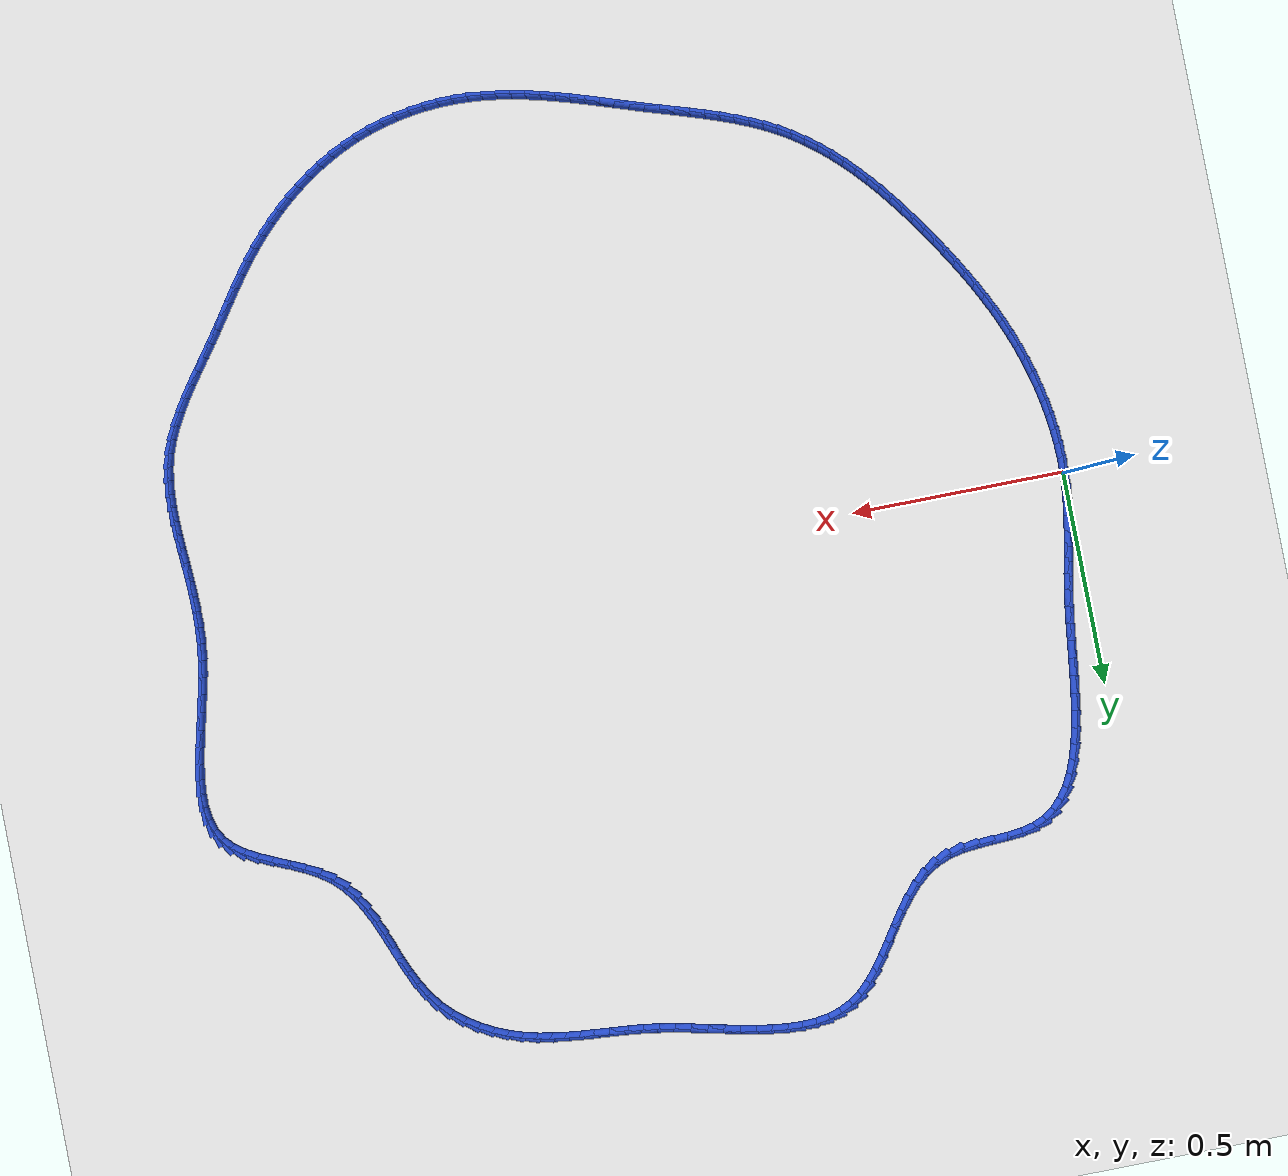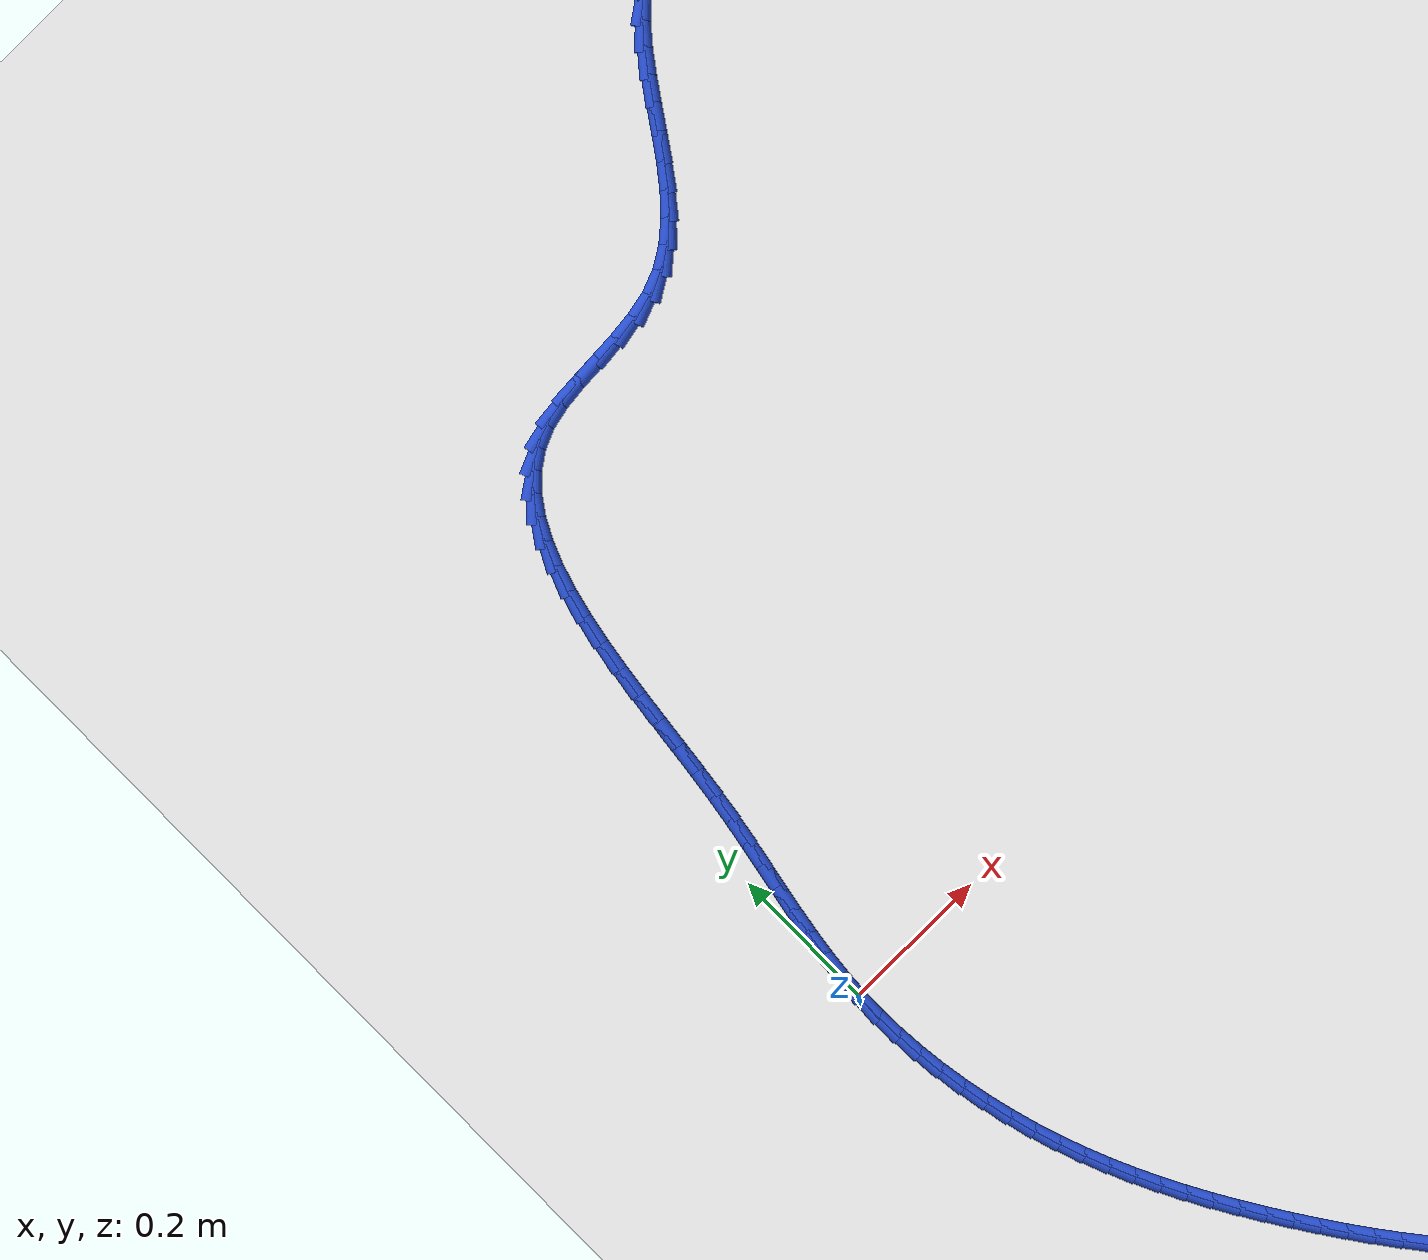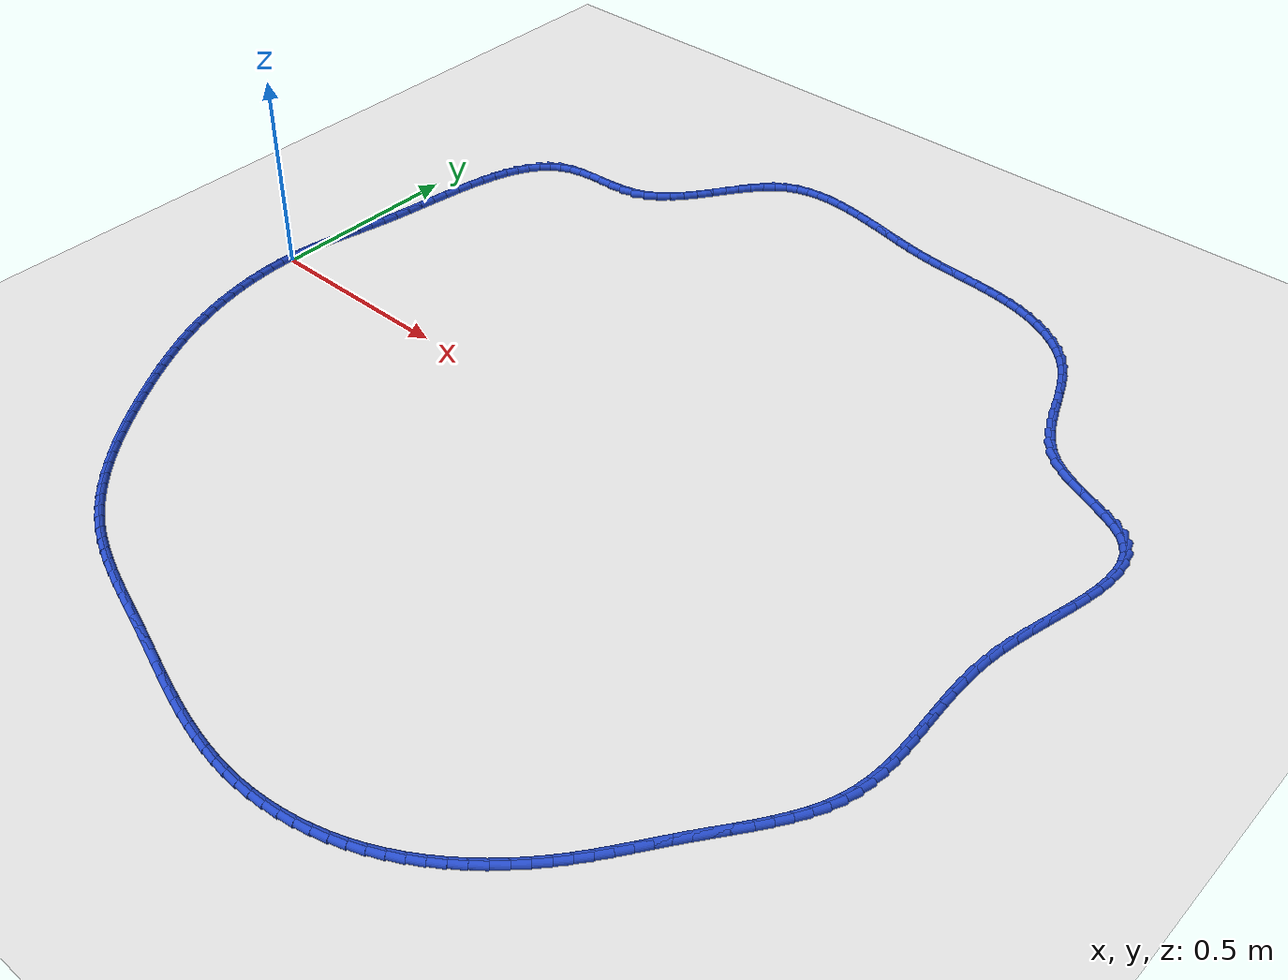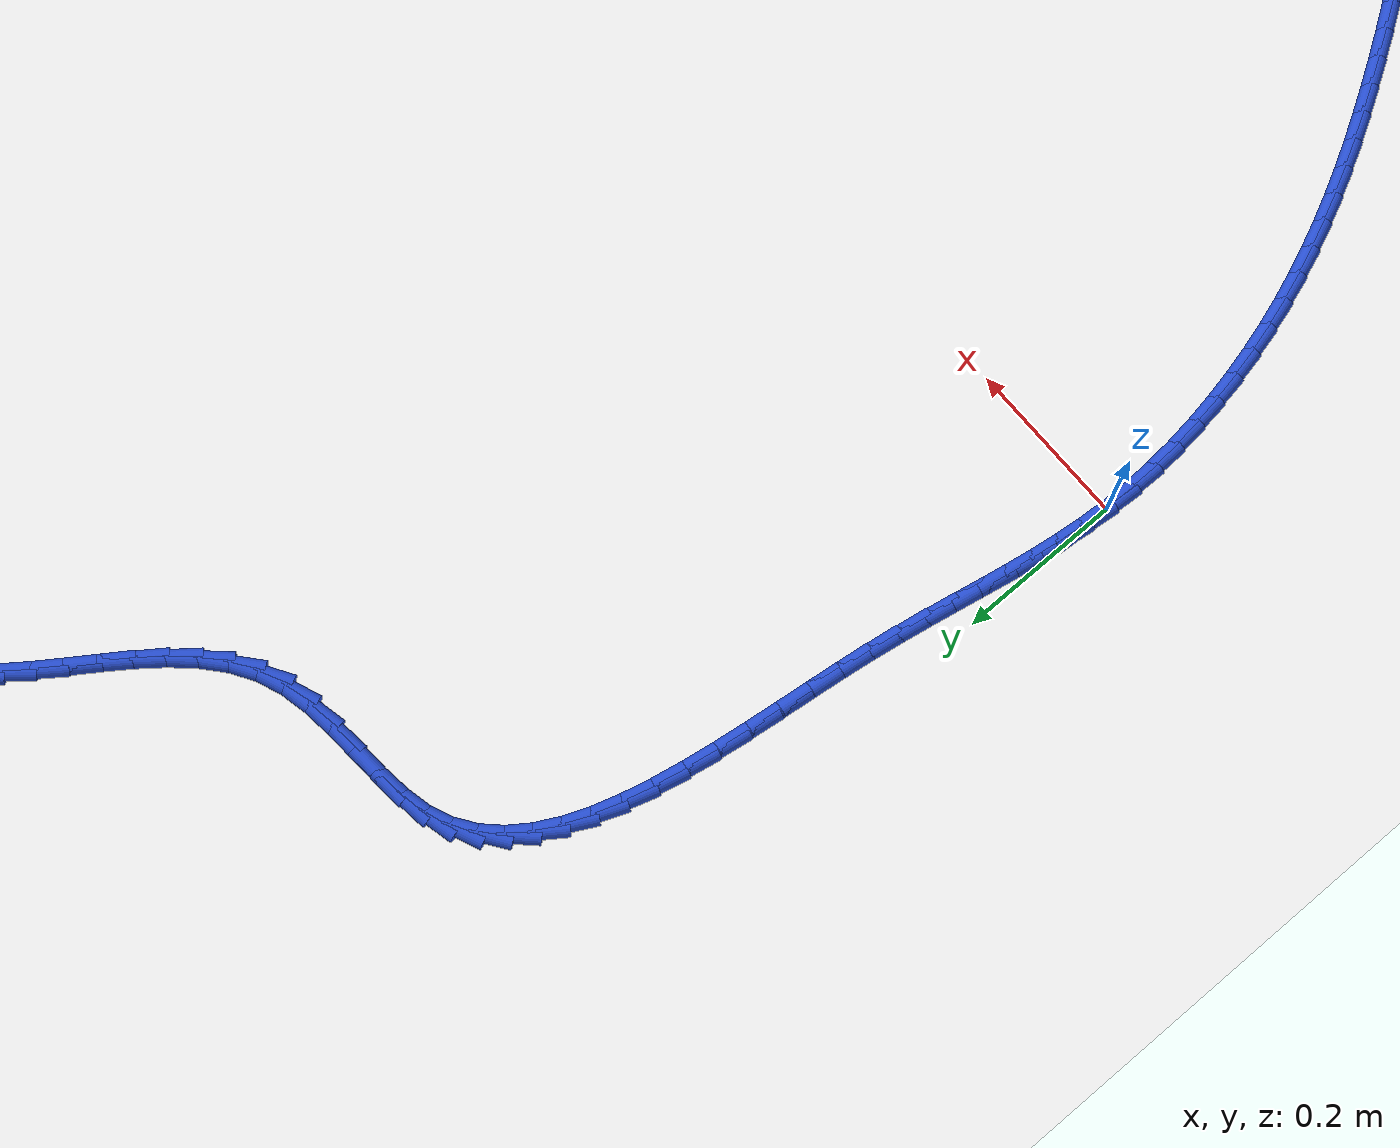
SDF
<sdf version="1.6">
 <world name="default">
  <light name="sun" type="directional">
   <pose>0 0 10 0 -0 0</pose>
   <diffuse>0.8 0.8 0.8 1</diffuse>
   <specular>0.2 0.2 0.2 1</specular>
   <attenuation>
    <range>1000</range>
    <constant>0.9</constant>
    <linear>0.01</linear>
    <quadratic>0.001</quadratic>
   </attenuation>
   <direction>-0.5 0.1 -0.9</direction>
  </light>
  <model name="ground_plane">
   <static>1</static>
   <link name="link">
    <collision name="collision">
     <geometry><plane><normal>0 0 1</normal><size>100 100</size></plane></geometry>
     <surface><friction><ode><mu>100</mu><mu2>50</mu2></ode></friction></surface>
    </collision>
    <visual name="visual">
     <cast_shadows>0</cast_shadows>
     <geometry><plane><normal>0 0 1</normal><size>100 100</size></plane></geometry>
     <material>
      <script><uri>file://media/materials/scripts/gazebo.material</uri><name>Gazebo/WhiteGlow</name></script>
     </material>
    </visual>
   </link>
  </model>
  <gravity>0 0 -9.8</gravity>
  <magnetic_field>6e-06 2.3e-05 -4.2e-05</magnetic_field>
  <atmosphere type="adiabatic"/>
  <physics name="default_physics" default="0" type="ode">
   <max_step_size>0.001</max_step_size>
   <real_time_factor>1</real_time_factor>
   <real_time_update_rate>1000</real_time_update_rate>
  </physics>
  <scene><ambient>0.4 0.4 0.4 1</ambient><background>0.7 0.7 0.7 1</background><shadows>1</shadows></scene>
  <spherical_coordinates>
   <surface_model>EARTH_WGS84</surface_model>
   <latitude_deg>0</latitude_deg>
   <longitude_deg>0</longitude_deg>
   <elevation>0</elevation>
   <heading_deg>0</heading_deg>
  </spherical_coordinates>
  <model name="line">
   <link name="link_0">
    <pose>-1.3877787807814457e-17 3.469446951953614e-17 0.01 0 1.57 1.5041577624133293</pose>
    <collision name="collision">
     <geometry><cylinder><radius>0.01</radius><length>0.08</length></cylinder></geometry>
    </collision>
    <visual name="visual">
     <material>
      <script><name>Gazebo/Blue</name><uri>file://media/materials/scripts/gazebo.material</uri></script>
     </material>
     <geometry><cylinder><radius>0.01</radius><length>0.08</length></cylinder></geometry>
    </visual>
   </link>
   <link name="link_1">
    <pose>0.0022216014161387993 0.03328871165796133 0.01 0 1.57 1.460614309213795</pose>
    <collision name="collision">
     <geometry><cylinder><radius>0.01</radius><length>0.08</length></cylinder></geometry>
    </collision>
    <visual name="visual">
     <material>
      <script><name>Gazebo/Blue</name><uri>file://media/materials/scripts/gazebo.material</uri></script>
     </material>
     <geometry><cylinder><radius>0.01</radius><length>0.08</length></cylinder></geometry>
    </visual>
   </link>
   <link name="link_2">
    <pose>0.005868797262017491 0.06625620387892209 0.01 0 1.57 1.4257154996217285</pose>
    <collision name="collision">
     <geometry><cylinder><radius>0.01</radius><length>0.08</length></cylinder></geometry>
    </collision>
    <visual name="visual">
     <material>
      <script><name>Gazebo/Blue</name><uri>file://media/materials/scripts/gazebo.material</uri></script>
     </material>
     <geometry><cylinder><radius>0.01</radius><length>0.08</length></cylinder></geometry>
    </visual>
   </link>
   <link name="link_3">
    <pose>0.01067267405056408 0.0991352877429741 0.01 0 1.57 1.400121704988857</pose>
    <collision name="collision">
     <geometry><cylinder><radius>0.01</radius><length>0.08</length></cylinder></geometry>
    </collision>
    <visual name="visual">
     <material>
      <script><name>Gazebo/Blue</name><uri>file://media/materials/scripts/gazebo.material</uri></script>
     </material>
     <geometry><cylinder><radius>0.01</radius><length>0.08</length></cylinder></geometry>
    </visual>
   </link>
   <link name="link_4">
    <pose>0.016364318294706602 0.13215877433020912 0.01 0 1.57 1.3840642982871783</pose>
    <collision name="collision">
     <geometry><cylinder><radius>0.01</radius><length>0.08</length></cylinder></geometry>
    </collision>
    <visual name="visual">
     <material>
      <script><name>Gazebo/Blue</name><uri>file://media/materials/scripts/gazebo.material</uri></script>
     </material>
     <geometry><cylinder><radius>0.01</radius><length>0.08</length></cylinder></geometry>
    </visual>
   </link>
   <link name="link_5">
    <pose>0.022674816507373064 0.16555947472071889 0.01 0 1.57 1.377410227121792</pose>
    <collision name="collision">
     <geometry><cylinder><radius>0.01</radius><length>0.08</length></cylinder></geometry>
    </collision>
    <visual name="visual">
     <material>
      <script><name>Gazebo/Blue</name><uri>file://media/materials/scripts/gazebo.material</uri></script>
     </material>
     <geometry><cylinder><radius>0.01</radius><length>0.08</length></cylinder></geometry>
    </visual>
   </link>
   <link name="link_6">
    <pose>0.029335255201491512 0.1995701999945952 0.01 0 1.57 1.3797331357902005</pose>
    <collision name="collision">
     <geometry><cylinder><radius>0.01</radius><length>0.08</length></cylinder></geometry>
    </collision>
    <visual name="visual">
     <material>
      <script><name>Gazebo/Blue</name><uri>file://media/materials/scripts/gazebo.material</uri></script>
     </material>
     <geometry><cylinder><radius>0.01</radius><length>0.08</length></cylinder></geometry>
    </visual>
   </link>
   <link name="link_7">
    <pose>0.03607672088998996 0.23442376123192987 0.01 0 1.57 1.390377217215085</pose>
    <collision name="collision">
     <geometry><cylinder><radius>0.01</radius><length>0.08</length></cylinder></geometry>
    </collision>
    <visual name="visual">
     <material>
      <script><name>Gazebo/Blue</name><uri>file://media/materials/scripts/gazebo.material</uri></script>
     </material>
     <geometry><cylinder><radius>0.01</radius><length>0.08</length></cylinder></geometry>
    </visual>
   </link>
   <link name="link_8">
    <pose>0.04263030008579644 0.27035296951281457 0.01 0 1.57 1.408510063824198</pose>
    <collision name="collision">
     <geometry><cylinder><radius>0.01</radius><length>0.08</length></cylinder></geometry>
    </collision>
    <visual name="visual">
     <material>
      <script><name>Gazebo/Blue</name><uri>file://media/materials/scripts/gazebo.material</uri></script>
     </material>
     <geometry><cylinder><radius>0.01</radius><length>0.08</length></cylinder></geometry>
    </visual>
   </link>
   <link name="link_9">
    <pose>0.04872707930183896 0.30759063591734104 0.01 0 1.57 1.4306113998912529</pose>
    <collision name="collision">
     <geometry><cylinder><radius>0.01</radius><length>0.08</length></cylinder></geometry>
    </collision>
    <visual name="visual">
     <material>
      <script><name>Gazebo/Blue</name><uri>file://media/materials/scripts/gazebo.material</uri></script>
     </material>
     <geometry><cylinder><radius>0.01</radius><length>0.08</length></cylinder></geometry>
    </visual>
   </link>
   <link name="link_10">
    <pose>0.054184597166854365 0.3462661270600283 0.01 0 1.57 1.4451936399020995</pose>
    <collision name="collision">
     <geometry><cylinder><radius>0.01</radius><length>0.08</length></cylinder></geometry>
    </collision>
    <visual name="visual">
     <material>
      <script><name>Gazebo/Blue</name><uri>file://media/materials/scripts/gazebo.material</uri></script>
     </material>
     <geometry><cylinder><radius>0.01</radius><length>0.08</length></cylinder></geometry>
    </visual>
   </link>
   <link name="link_11">
    <pose>0.05920745579965627 0.3860456679017837 0.01 0 1.57 1.450132228644873</pose>
    <collision name="collision">
     <geometry><cylinder><radius>0.01</radius><length>0.08</length></cylinder></geometry>
    </collision>
    <visual name="visual">
     <material>
      <script><name>Gazebo/Blue</name><uri>file://media/materials/scripts/gazebo.material</uri></script>
     </material>
     <geometry><cylinder><radius>0.01</radius><length>0.08</length></cylinder></geometry>
    </visual>
   </link>
   <link name="link_12">
    <pose>0.0641085384176914 0.42646591942147716 0.01 0 1.57 1.4460171008260039</pose>
    <collision name="collision">
     <geometry><cylinder><radius>0.01</radius><length>0.08</length></cylinder></geometry>
    </collision>
    <visual name="visual">
     <material>
      <script><name>Gazebo/Blue</name><uri>file://media/materials/scripts/gazebo.material</uri></script>
     </material>
     <geometry><cylinder><radius>0.01</radius><length>0.08</length></cylinder></geometry>
    </visual>
   </link>
   <link name="link_13">
    <pose>0.06920073336715214 0.46706353646116755 0.01 0 1.57 1.432854624688631</pose>
    <collision name="collision">
     <geometry><cylinder><radius>0.01</radius><length>0.08</length></cylinder></geometry>
    </collision>
    <visual name="visual">
     <material>
      <script><name>Gazebo/Blue</name><uri>file://media/materials/scripts/gazebo.material</uri></script>
     </material>
     <geometry><cylinder><radius>0.01</radius><length>0.08</length></cylinder></geometry>
    </visual>
   </link>
   <link name="link_14">
    <pose>0.07479692899423082 0.5073751738629132 0.01 0 1.57 1.4100933242397045</pose>
    <collision name="collision">
     <geometry><cylinder><radius>0.01</radius><length>0.08</length></cylinder></geometry>
    </collision>
    <visual name="visual">
     <material>
      <script><name>Gazebo/Blue</name><uri>file://media/materials/scripts/gazebo.material</uri></script>
     </material>
     <geometry><cylinder><radius>0.01</radius><length>0.08</length></cylinder></geometry>
    </visual>
   </link>
   <link name="link_15">
    <pose>0.08121001364511976 0.5469374864687723 0.01 0 1.57 1.3765887190114745</pose>
    <collision name="collision">
     <geometry><cylinder><radius>0.01</radius><length>0.08</length></cylinder></geometry>
    </collision>
    <visual name="visual">
     <material>
      <script><name>Gazebo/Blue</name><uri>file://media/materials/scripts/gazebo.material</uri></script>
     </material>
     <geometry><cylinder><radius>0.01</radius><length>0.08</length></cylinder></geometry>
    </visual>
   </link>
   <link name="link_16">
    <pose>0.08875287566601131 0.5852871291208035 0.01 0 1.57 1.3305164755266785</pose>
    <collision name="collision">
     <geometry><cylinder><radius>0.01</radius><length>0.08</length></cylinder></geometry>
    </collision>
    <visual name="visual">
     <material>
      <script><name>Gazebo/Blue</name><uri>file://media/materials/scripts/gazebo.material</uri></script>
     </material>
     <geometry><cylinder><radius>0.01</radius><length>0.08</length></cylinder></geometry>
    </visual>
   </link>
   <link name="link_17">
    <pose>0.09773840340309785 0.6219607566610653 0.01 0 1.57 1.2692541753248683</pose>
    <collision name="collision">
     <geometry><cylinder><radius>0.01</radius><length>0.08</length></cylinder></geometry>
    </collision>
    <visual name="visual">
     <material>
      <script><name>Gazebo/Blue</name><uri>file://media/materials/scripts/gazebo.material</uri></script>
     </material>
     <geometry><cylinder><radius>0.01</radius><length>0.08</length></cylinder></geometry>
    </visual>
   </link>
   <link name="link_18">
    <pose>0.10847948520257168 0.656495023931616 0.01 0 1.57 1.1892941572460245</pose>
    <collision name="collision">
     <geometry><cylinder><radius>0.01</radius><length>0.08</length></cylinder></geometry>
    </collision>
    <visual name="visual">
     <material>
      <script><name>Gazebo/Blue</name><uri>file://media/materials/scripts/gazebo.material</uri></script>
     </material>
     <geometry><cylinder><radius>0.01</radius><length>0.08</length></cylinder></geometry>
    </visual>
   </link>
   <link name="link_19">
    <pose>0.12128900941062515 0.6884265857745141 0.01 0 1.57 1.0863596173549557</pose>
    <collision name="collision">
     <geometry><cylinder><radius>0.01</radius><length>0.08</length></cylinder></geometry>
    </collision>
    <visual name="visual">
     <material>
      <script><name>Gazebo/Blue</name><uri>file://media/materials/scripts/gazebo.material</uri></script>
     </material>
     <geometry><cylinder><radius>0.01</radius><length>0.08</length></cylinder></geometry>
    </visual>
   </link>
   <link name="link_20">
    <pose>0.13647986437345067 0.717292097031818 0.01 0 1.57 0.9561134272143081</pose>
    <collision name="collision">
     <geometry><cylinder><radius>0.01</radius><length>0.08</length></cylinder></geometry>
    </collision>
    <visual name="visual">
     <material>
      <script><name>Gazebo/Blue</name><uri>file://media/materials/scripts/gazebo.material</uri></script>
     </material>
     <geometry><cylinder><radius>0.01</radius><length>0.08</length></cylinder></geometry>
    </visual>
   </link>
   <link name="link_21">
    <pose>0.15436493843724047 0.7426282125455862 0.01 0 1.57 0.7960805357936478</pose>
    <collision name="collision">
     <geometry><cylinder><radius>0.01</radius><length>0.08</length></cylinder></geometry>
    </collision>
    <visual name="visual">
     <material>
      <script><name>Gazebo/Blue</name><uri>file://media/materials/scripts/gazebo.material</uri></script>
     </material>
     <geometry><cylinder><radius>0.01</radius><length>0.08</length></cylinder></geometry>
    </visual>
   </link>
   <link name="link_22">
    <pose>0.17525711994818705 0.7639715871578772 0.01 0 1.57 0.6090265492266352</pose>
    <collision name="collision">
     <geometry><cylinder><radius>0.01</radius><length>0.08</length></cylinder></geometry>
    </collision>
    <visual name="visual">
     <material>
      <script><name>Gazebo/Blue</name><uri>file://media/materials/scripts/gazebo.material</uri></script>
     </material>
     <geometry><cylinder><radius>0.01</radius><length>0.08</length></cylinder></geometry>
    </visual>
   </link>
   <link name="link_23">
    <pose>0.19946929725248266 0.7808588757107495 0.01 0 1.57 0.4059798487005549</pose>
    <collision name="collision">
     <geometry><cylinder><radius>0.01</radius><length>0.08</length></cylinder></geometry>
    </collision>
    <visual name="visual">
     <material>
      <script><name>Gazebo/Blue</name><uri>file://media/materials/scripts/gazebo.material</uri></script>
     </material>
     <geometry><cylinder><radius>0.01</radius><length>0.08</length></cylinder></geometry>
    </visual>
   </link>
   <link name="link_24">
    <pose>0.22731354627591618 0.7928280029404364 0.01 0 1.57 0.2231014780276281</pose>
    <collision name="collision">
     <geometry><cylinder><radius>0.01</radius><length>0.08</length></cylinder></geometry>
    </collision>
    <visual name="visual">
     <material>
      <script><name>Gazebo/Blue</name><uri>file://media/materials/scripts/gazebo.material</uri></script>
     </material>
     <geometry><cylinder><radius>0.01</radius><length>0.08</length></cylinder></geometry>
    </visual>
   </link>
   <link name="link_25">
    <pose>0.2587537791636702 0.7999611083216062 0.01 0 1.57 0.11003937888747167</pose>
    <collision name="collision">
     <geometry><cylinder><radius>0.01</radius><length>0.08</length></cylinder></geometry>
    </collision>
    <visual name="visual">
     <material>
      <script><name>Gazebo/Blue</name><uri>file://media/materials/scripts/gazebo.material</uri></script>
     </material>
     <geometry><cylinder><radius>0.01</radius><length>0.08</length></cylinder></geometry>
    </visual>
   </link>
   <link name="link_26">
    <pose>0.29286492438994505 0.8037299015338724 0.01 0 1.57 0.058582114916161374</pose>
    <collision name="collision">
     <geometry><cylinder><radius>0.01</radius><length>0.08</length></cylinder></geometry>
    </collision>
    <visual name="visual">
     <material>
      <script><name>Gazebo/Blue</name><uri>file://media/materials/scripts/gazebo.material</uri></script>
     </material>
     <geometry><cylinder><radius>0.01</radius><length>0.08</length></cylinder></geometry>
    </visual>
   </link>
   <link name="link_27">
    <pose>0.32858206534871304 0.8058246840748297 0.01 0 1.57 0.05815764598075501</pose>
    <collision name="collision">
     <geometry><cylinder><radius>0.01</radius><length>0.08</length></cylinder></geometry>
    </collision>
    <visual name="visual">
     <material>
      <script><name>Gazebo/Blue</name><uri>file://media/materials/scripts/gazebo.material</uri></script>
     </material>
     <geometry><cylinder><radius>0.01</radius><length>0.08</length></cylinder></geometry>
    </visual>
   </link>
   <link name="link_28">
    <pose>0.364840285433946 0.8079357574420722 0.01 0 1.57 0.10643082712850482</pose>
    <collision name="collision">
     <geometry><cylinder><radius>0.01</radius><length>0.08</length></cylinder></geometry>
    </collision>
    <visual name="visual">
     <material>
      <script><name>Gazebo/Blue</name><uri>file://media/materials/scripts/gazebo.material</uri></script>
     </material>
     <geometry><cylinder><radius>0.01</radius><length>0.08</length></cylinder></geometry>
    </visual>
   </link>
   <link name="link_29">
    <pose>0.4005746680396163 0.8117534231331952 0.01 0 1.57 0.2082254150575818</pose>
    <collision name="collision">
     <geometry><cylinder><radius>0.01</radius><length>0.08</length></cylinder></geometry>
    </collision>
    <visual name="visual">
     <material>
      <script><name>Gazebo/Blue</name><uri>file://media/materials/scripts/gazebo.material</uri></script>
     </material>
     <geometry><cylinder><radius>0.01</radius><length>0.08</length></cylinder></geometry>
    </visual>
   </link>
   <link name="link_30">
    <pose>0.43472029655969624 0.8189679826457921 0.01 0 1.57 0.3712065709629593</pose>
    <collision name="collision">
     <geometry><cylinder><radius>0.01</radius><length>0.08</length></cylinder></geometry>
    </collision>
    <visual name="visual">
     <material>
      <script><name>Gazebo/Blue</name><uri>file://media/materials/scripts/gazebo.material</uri></script>
     </material>
     <geometry><cylinder><radius>0.01</radius><length>0.08</length></cylinder></geometry>
    </visual>
   </link>
   <link name="link_31">
    <pose>0.4662327787159836 0.8312342761080657 0.01 0 1.57 0.558101284543423</pose>
    <collision name="collision">
     <geometry><cylinder><radius>0.01</radius><length>0.08</length></cylinder></geometry>
    </collision>
    <visual name="visual">
     <material>
      <script><name>Gazebo/Blue</name><uri>file://media/materials/scripts/gazebo.material</uri></script>
     </material>
     <geometry><cylinder><radius>0.01</radius><length>0.08</length></cylinder></geometry>
    </visual>
   </link>
   <link name="link_32">
    <pose>0.49474597275948046 0.8490352810293224 0.01 0 1.57 0.7119532725827579</pose>
    <collision name="collision">
     <geometry><cylinder><radius>0.01</radius><length>0.08</length></cylinder></geometry>
    </collision>
    <visual name="visual">
     <material>
      <script><name>Gazebo/Blue</name><uri>file://media/materials/scripts/gazebo.material</uri></script>
     </material>
     <geometry><cylinder><radius>0.01</radius><length>0.08</length></cylinder></geometry>
    </visual>
   </link>
   <link name="link_33">
    <pose>0.5207112431086849 0.8714415102363451 0.01 0 1.57 0.8270540318147703</pose>
    <collision name="collision">
     <geometry><cylinder><radius>0.01</radius><length>0.08</length></cylinder></geometry>
    </collision>
    <visual name="visual">
     <material>
      <script><name>Gazebo/Blue</name><uri>file://media/materials/scripts/gazebo.material</uri></script>
     </material>
     <geometry><cylinder><radius>0.01</radius><length>0.08</length></cylinder></geometry>
    </visual>
   </link>
   <link name="link_34">
    <pose>0.5446286344524531 0.8974393681230386 0.01 0 1.57 0.9066239495584035</pose>
    <collision name="collision">
     <geometry><cylinder><radius>0.01</radius><length>0.08</length></cylinder></geometry>
    </collision>
    <visual name="visual">
     <material>
      <script><name>Gazebo/Blue</name><uri>file://media/materials/scripts/gazebo.material</uri></script>
     </material>
     <geometry><cylinder><radius>0.01</radius><length>0.08</length></cylinder></geometry>
    </visual>
   </link>
   <link name="link_35">
    <pose>0.5669981914796409 0.9260152590833077 0.01 0 1.57 0.9551101302700191</pose>
    <collision name="collision">
     <geometry><cylinder><radius>0.01</radius><length>0.08</length></cylinder></geometry>
    </collision>
    <visual name="visual">
     <material>
      <script><name>Gazebo/Blue</name><uri>file://media/materials/scripts/gazebo.material</uri></script>
     </material>
     <geometry><cylinder><radius>0.01</radius><length>0.08</length></cylinder></geometry>
    </visual>
   </link>
   <link name="link_36">
    <pose>0.5883199588791046 0.9561555875110571 0.01 0 1.57 0.9757610906334523</pose>
    <collision name="collision">
     <geometry><cylinder><radius>0.01</radius><length>0.08</length></cylinder></geometry>
    </collision>
    <visual name="visual">
     <material>
      <script><name>Gazebo/Blue</name><uri>file://media/materials/scripts/gazebo.material</uri></script>
     </material>
     <geometry><cylinder><radius>0.01</radius><length>0.08</length></cylinder></geometry>
    </visual>
   </link>
   <link name="link_37">
    <pose>0.6090939813397004 0.9868467578001916 0.01 0 1.57 0.9697616096306702</pose>
    <collision name="collision">
     <geometry><cylinder><radius>0.01</radius><length>0.08</length></cylinder></geometry>
    </collision>
    <visual name="visual">
     <material>
      <script><name>Gazebo/Blue</name><uri>file://media/materials/scripts/gazebo.material</uri></script>
     </material>
     <geometry><cylinder><radius>0.01</radius><length>0.08</length></cylinder></geometry>
    </visual>
   </link>
   <link name="link_38">
    <pose>0.6298203035502841 1.0170751743446156 0.01 0 1.57 0.93592891255605</pose>
    <collision name="collision">
     <geometry><cylinder><radius>0.01</radius><length>0.08</length></cylinder></geometry>
    </collision>
    <visual name="visual">
     <material>
      <script><name>Gazebo/Blue</name><uri>file://media/materials/scripts/gazebo.material</uri></script>
     </material>
     <geometry><cylinder><radius>0.01</radius><length>0.08</length></cylinder></geometry>
    </visual>
   </link>
   <link name="link_39">
    <pose>0.6509989701997118 1.045827241538234 0.01 0 1.57 0.8705563560619634</pose>
    <collision name="collision">
     <geometry><cylinder><radius>0.01</radius><length>0.08</length></cylinder></geometry>
    </collision>
    <visual name="visual">
     <material>
      <script><name>Gazebo/Blue</name><uri>file://media/materials/scripts/gazebo.material</uri></script>
     </material>
     <geometry><cylinder><radius>0.01</radius><length>0.08</length></cylinder></geometry>
    </visual>
   </link>
   <link name="link_40">
    <pose>0.6731300259768396 1.0720893637749513 0.01 0 1.57 0.767599631983861</pose>
    <collision name="collision">
     <geometry><cylinder><radius>0.01</radius><length>0.08</length></cylinder></geometry>
    </collision>
    <visual name="visual">
     <material>
      <script><name>Gazebo/Blue</name><uri>file://media/materials/scripts/gazebo.material</uri></script>
     </material>
     <geometry><cylinder><radius>0.01</radius><length>0.08</length></cylinder></geometry>
    </visual>
   </link>
   <link name="link_41">
    <pose>0.6967135155705237 1.0948479454486724 0.01 0 1.57 0.620652015036451</pose>
    <collision name="collision">
     <geometry><cylinder><radius>0.01</radius><length>0.08</length></cylinder></geometry>
    </collision>
    <visual name="visual">
     <material>
      <script><name>Gazebo/Blue</name><uri>file://media/materials/scripts/gazebo.material</uri></script>
     </material>
     <geometry><cylinder><radius>0.01</radius><length>0.08</length></cylinder></geometry>
    </visual>
   </link>
   <link name="link_42">
    <pose>0.7222445313142545 1.1130999100606684 0.01 0 1.57 0.4482213147575738</pose>
    <collision name="collision">
     <geometry><cylinder><radius>0.01</radius><length>0.08</length></cylinder></geometry>
    </collision>
    <visual name="visual">
     <material>
      <script><name>Gazebo/Blue</name><uri>file://media/materials/scripts/gazebo.material</uri></script>
     </material>
     <geometry><cylinder><radius>0.01</radius><length>0.08</length></cylinder></geometry>
    </visual>
   </link>
   <link name="link_43">
    <pose>0.7499459040268344 1.1264204813134737 0.01 0 1.57 0.289160623994503</pose>
    <collision name="collision">
     <geometry><cylinder><radius>0.01</radius><length>0.08</length></cylinder></geometry>
    </collision>
    <visual name="visual">
     <material>
      <script><name>Gazebo/Blue</name><uri>file://media/materials/scripts/gazebo.material</uri></script>
     </material>
     <geometry><cylinder><radius>0.01</radius><length>0.08</length></cylinder></geometry>
    </visual>
   </link>
   <link name="link_44">
    <pose>0.7796321753796946 1.1352521141683964 0.01 0 1.57 0.15319760592363502</pose>
    <collision name="collision">
     <geometry><cylinder><radius>0.01</radius><length>0.08</length></cylinder></geometry>
    </collision>
    <visual name="visual">
     <material>
      <script><name>Gazebo/Blue</name><uri>file://media/materials/scripts/gazebo.material</uri></script>
     </material>
     <geometry><cylinder><radius>0.01</radius><length>0.08</length></cylinder></geometry>
    </visual>
   </link>
   <link name="link_45">
    <pose>0.8110843209900218 1.1401085599502714 0.01 0 1.57 0.04224916205095813</pose>
    <collision name="collision">
     <geometry><cylinder><radius>0.01</radius><length>0.08</length></cylinder></geometry>
    </collision>
    <visual name="visual">
     <material>
      <script><name>Gazebo/Blue</name><uri>file://media/materials/scripts/gazebo.material</uri></script>
     </material>
     <geometry><cylinder><radius>0.01</radius><length>0.08</length></cylinder></geometry>
    </visual>
   </link>
   <link name="link_46">
    <pose>0.8440833164750022 1.1415035699839324 0.01 0 1.57 -0.045201295922695624</pose>
    <collision name="collision">
     <geometry><cylinder><radius>0.01</radius><length>0.08</length></cylinder></geometry>
    </collision>
    <visual name="visual">
     <material>
      <script><name>Gazebo/Blue</name><uri>file://media/materials/scripts/gazebo.material</uri></script>
     </material>
     <geometry><cylinder><radius>0.01</radius><length>0.08</length></cylinder></geometry>
    </visual>
   </link>
   <link name="link_47">
    <pose>0.8784101374518226 1.1399508955942144 0.01 0 1.57 -0.11203174927479957</pose>
    <collision name="collision">
     <geometry><cylinder><radius>0.01</radius><length>0.08</length></cylinder></geometry>
    </collision>
    <visual name="visual">
     <material>
      <script><name>Gazebo/Blue</name><uri>file://media/materials/scripts/gazebo.material</uri></script>
     </material>
     <geometry><cylinder><radius>0.01</radius><length>0.08</length></cylinder></geometry>
    </visual>
   </link>
   <link name="link_48">
    <pose>0.9138457595376692 1.1359642881059522 0.01 0 1.57 -0.16119682417151132</pose>
    <collision name="collision">
     <geometry><cylinder><radius>0.01</radius><length>0.08</length></cylinder></geometry>
    </collision>
    <visual name="visual">
     <material>
      <script><name>Gazebo/Blue</name><uri>file://media/materials/scripts/gazebo.material</uri></script>
     </material>
     <geometry><cylinder><radius>0.01</radius><length>0.08</length></cylinder></geometry>
    </visual>
   </link>
   <link name="link_49">
    <pose>0.950171158349729 1.1300574988439802 0.01 0 1.57 -0.19515913053303435</pose>
    <collision name="collision">
     <geometry><cylinder><radius>0.01</radius><length>0.08</length></cylinder></geometry>
    </collision>
    <visual name="visual">
     <material>
      <script><name>Gazebo/Blue</name><uri>file://media/materials/scripts/gazebo.material</uri></script>
     </material>
     <geometry><cylinder><radius>0.01</radius><length>0.08</length></cylinder></geometry>
    </visual>
   </link>
   <link name="link_50">
    <pose>0.987167309505188 1.1227442791331326 0.01 0 1.57 -0.21571891843026414</pose>
    <collision name="collision">
     <geometry><cylinder><radius>0.01</radius><length>0.08</length></cylinder></geometry>
    </collision>
    <visual name="visual">
     <material>
      <script><name>Gazebo/Blue</name><uri>file://media/materials/scripts/gazebo.material</uri></script>
     </material>
     <geometry><cylinder><radius>0.01</radius><length>0.08</length></cylinder></geometry>
    </visual>
   </link>
   <link name="link_51">
    <pose>1.024615188621233 1.1145383802982438 0.01 0 1.57 -0.22400793966190222</pose>
    <collision name="collision">
     <geometry><cylinder><radius>0.01</radius><length>0.08</length></cylinder></geometry>
    </collision>
    <visual name="visual">
     <material>
      <script><name>Gazebo/Blue</name><uri>file://media/materials/scripts/gazebo.material</uri></script>
     </material>
     <geometry><cylinder><radius>0.01</radius><length>0.08</length></cylinder></geometry>
    </visual>
   </link>
   <link name="link_52">
    <pose>1.0622957713150498 1.105953553664149 0.01 0 1.57 -0.22052632753357507</pose>
    <collision name="collision">
     <geometry><cylinder><radius>0.01</radius><length>0.08</length></cylinder></geometry>
    </collision>
    <visual name="visual">
     <material>
      <script><name>Gazebo/Blue</name><uri>file://media/materials/scripts/gazebo.material</uri></script>
     </material>
     <geometry><cylinder><radius>0.01</radius><length>0.08</length></cylinder></geometry>
    </visual>
   </link>
   <link name="link_53">
    <pose>1.0999900332038257 1.0975035505556825 0.01 0 1.57 -0.20517136011554662</pose>
    <collision name="collision">
     <geometry><cylinder><radius>0.01</radius><length>0.08</length></cylinder></geometry>
    </collision>
    <visual name="visual">
     <material>
      <script><name>Gazebo/Blue</name><uri>file://media/materials/scripts/gazebo.material</uri></script>
     </material>
     <geometry><cylinder><radius>0.01</radius><length>0.08</length></cylinder></geometry>
    </visual>
   </link>
   <link name="link_54">
    <pose>1.137478949904747 1.0897021222976788 0.01 0 1.57 -0.17724304943913022</pose>
    <collision name="collision">
     <geometry><cylinder><radius>0.01</radius><length>0.08</length></cylinder></geometry>
    </collision>
    <visual name="visual">
     <material>
      <script><name>Gazebo/Blue</name><uri>file://media/materials/scripts/gazebo.material</uri></script>
     </material>
     <geometry><cylinder><radius>0.01</radius><length>0.08</length></cylinder></geometry>
    </visual>
   </link>
   <link name="link_55">
    <pose>1.174543497035 1.0830630202149722 0.01 0 1.57 -0.1396578547185494</pose>
    <collision name="collision">
     <geometry><cylinder><radius>0.01</radius><length>0.08</length></cylinder></geometry>
    </collision>
    <visual name="visual">
     <material>
      <script><name>Gazebo/Blue</name><uri>file://media/materials/scripts/gazebo.material</uri></script>
     </material>
     <geometry><cylinder><radius>0.01</radius><length>0.08</length></cylinder></geometry>
    </visual>
   </link>
   <link name="link_56">
    <pose>1.2110076473723592 1.0779371462353102 0.01 0 1.57 -0.10868754454958968</pose>
    <collision name="collision">
     <geometry><cylinder><radius>0.01</radius><length>0.08</length></cylinder></geometry>
    </collision>
    <visual name="visual">
     <material>
      <script><name>Gazebo/Blue</name><uri>file://media/materials/scripts/gazebo.material</uri></script>
     </material>
     <geometry><cylinder><radius>0.01</radius><length>0.08</length></cylinder></geometry>
    </visual>
   </link>
   <link name="link_57">
    <pose>1.2468673032739161 1.074024228396105 0.01 0 1.57 -0.0893789697139297</pose>
    <collision name="collision">
     <geometry><cylinder><radius>0.01</radius><length>0.08</length></cylinder></geometry>
    </collision>
    <visual name="visual">
     <material>
      <script><name>Gazebo/Blue</name><uri>file://media/materials/scripts/gazebo.material</uri></script>
     </material>
     <geometry><cylinder><radius>0.01</radius><length>0.08</length></cylinder></geometry>
    </visual>
   </link>
   <link name="link_58">
    <pose>1.282161334730905 1.0708612571674843 0.01 0 1.57 -0.0825345256419253</pose>
    <collision name="collision">
     <geometry><cylinder><radius>0.01</radius><length>0.08</length></cylinder></geometry>
    </collision>
    <visual name="visual">
     <material>
      <script><name>Gazebo/Blue</name><uri>file://media/materials/scripts/gazebo.material</uri></script>
     </material>
     <geometry><cylinder><radius>0.01</radius><length>0.08</length></cylinder></geometry>
    </visual>
   </link>
   <link name="link_59">
    <pose>1.3169286117345602 1.067985223019575 0.01 0 1.57 -0.08880202893705323</pose>
    <collision name="collision">
     <geometry><cylinder><radius>0.01</radius><length>0.08</length></cylinder></geometry>
    </collision>
    <visual name="visual">
     <material>
      <script><name>Gazebo/Blue</name><uri>file://media/materials/scripts/gazebo.material</uri></script>
     </material>
     <geometry><cylinder><radius>0.01</radius><length>0.08</length></cylinder></geometry>
    </visual>
   </link>
   <link name="link_60">
    <pose>1.351208004276115 1.064933116422505 0.01 0 1.57 -0.10867879760519396</pose>
    <collision name="collision">
     <geometry><cylinder><radius>0.01</radius><length>0.08</length></cylinder></geometry>
    </collision>
    <visual name="visual">
     <material>
      <script><name>Gazebo/Blue</name><uri>file://media/materials/scripts/gazebo.material</uri></script>
     </material>
     <geometry><cylinder><radius>0.01</radius><length>0.08</length></cylinder></geometry>
    </visual>
   </link>
   <link name="link_61">
    <pose>1.3850383823468033 1.0612419278464016 0.01 0 1.57 -0.14245301429784252</pose>
    <collision name="collision">
     <geometry><cylinder><radius>0.01</radius><length>0.08</length></cylinder></geometry>
    </collision>
    <visual name="visual">
     <material>
      <script><name>Gazebo/Blue</name><uri>file://media/materials/scripts/gazebo.material</uri></script>
     </material>
     <geometry><cylinder><radius>0.01</radius><length>0.08</length></cylinder></geometry>
    </visual>
   </link>
   <link name="link_62">
    <pose>1.4184586159378587 1.056448647761392 0.01 0 1.57 -0.19007033997776585</pose>
    <collision name="collision">
     <geometry><cylinder><radius>0.01</radius><length>0.08</length></cylinder></geometry>
    </collision>
    <visual name="visual">
     <material>
      <script><name>Gazebo/Blue</name><uri>file://media/materials/scripts/gazebo.material</uri></script>
     </material>
     <geometry><cylinder><radius>0.01</radius><length>0.08</length></cylinder></geometry>
    </visual>
   </link>
   <link name="link_63">
    <pose>1.4515075750405153 1.0500902666376033 0.01 0 1.57 -0.25093475802618304</pose>
    <collision name="collision">
     <geometry><cylinder><radius>0.01</radius><length>0.08</length></cylinder></geometry>
    </collision>
    <visual name="visual">
     <material>
      <script><name>Gazebo/Blue</name><uri>file://media/materials/scripts/gazebo.material</uri></script>
     </material>
     <geometry><cylinder><radius>0.01</radius><length>0.08</length></cylinder></geometry>
    </visual>
   </link>
   <link name="link_64">
    <pose>1.4842241296460057 1.0417037749451634 0.01 0 1.57 -0.32368742261113354</pose>
    <collision name="collision">
     <geometry><cylinder><radius>0.01</radius><length>0.08</length></cylinder></geometry>
    </collision>
    <visual name="visual">
     <material>
      <script><name>Gazebo/Blue</name><uri>file://media/materials/scripts/gazebo.material</uri></script>
     </material>
     <geometry><cylinder><radius>0.01</radius><length>0.08</length></cylinder></geometry>
    </visual>
   </link>
   <link name="link_65">
    <pose>1.516646865301825 1.0308263750430855 0.01 0 1.57 -0.4047346980435109</pose>
    <collision name="collision">
     <geometry><cylinder><radius>0.01</radius><length>0.08</length></cylinder></geometry>
    </collision>
    <visual name="visual">
     <material>
      <script><name>Gazebo/Blue</name><uri>file://media/materials/scripts/gazebo.material</uri></script>
     </material>
     <geometry><cylinder><radius>0.01</radius><length>0.08</length></cylinder></geometry>
    </visual>
   </link>
   <link name="link_66">
    <pose>1.5486532046436847 1.017115323364046 0.01 0 1.57 -0.49030531913043446</pose>
    <collision name="collision">
     <geometry><cylinder><radius>0.01</radius><length>0.08</length></cylinder></geometry>
    </collision>
    <visual name="visual">
     <material>
      <script><name>Gazebo/Blue</name><uri>file://media/materials/scripts/gazebo.material</uri></script>
     </material>
     <geometry><cylinder><radius>0.01</radius><length>0.08</length></cylinder></geometry>
    </visual>
   </link>
   <link name="link_67">
    <pose>1.5796906055363609 1.000548167291743 0.01 0 1.57 -0.5824067748936377</pose>
    <collision name="collision">
     <geometry><cylinder><radius>0.01</radius><length>0.08</length></cylinder></geometry>
    </collision>
    <visual name="visual">
     <material>
      <script><name>Gazebo/Blue</name><uri>file://media/materials/scripts/gazebo.material</uri></script>
     </material>
     <geometry><cylinder><radius>0.01</radius><length>0.08</length></cylinder></geometry>
    </visual>
   </link>
   <link name="link_68">
    <pose>1.6091355976981119 0.9811552902677027 0.01 0 1.57 -0.683743074604117</pose>
    <collision name="collision">
     <geometry><cylinder><radius>0.01</radius><length>0.08</length></cylinder></geometry>
    </collision>
    <visual name="visual">
     <material>
      <script><name>Gazebo/Blue</name><uri>file://media/materials/scripts/gazebo.material</uri></script>
     </material>
     <geometry><cylinder><radius>0.01</radius><length>0.08</length></cylinder></geometry>
    </visual>
   </link>
   <link name="link_69">
    <pose>1.6363647108471966 0.9589670757334521 0.01 0 1.57 -0.796815812038557</pose>
    <collision name="collision">
     <geometry><cylinder><radius>0.01</radius><length>0.08</length></cylinder></geometry>
    </collision>
    <visual name="visual">
     <material>
      <script><name>Gazebo/Blue</name><uri>file://media/materials/scripts/gazebo.material</uri></script>
     </material>
     <geometry><cylinder><radius>0.01</radius><length>0.08</length></cylinder></geometry>
    </visual>
   </link>
   <link name="link_70">
    <pose>1.6607544747018737 0.9340139071305178 0.01 0 1.57 -0.9211903502369259</pose>
    <collision name="collision">
     <geometry><cylinder><radius>0.01</radius><length>0.08</length></cylinder></geometry>
    </collision>
    <visual name="visual">
     <material>
      <script><name>Gazebo/Blue</name><uri>file://media/materials/scripts/gazebo.material</uri></script>
     </material>
     <geometry><cylinder><radius>0.01</radius><length>0.08</length></cylinder></geometry>
    </visual>
   </link>
   <link name="link_71">
    <pose>1.6817608966522364 0.9063586988672996 0.01 0 1.57 -1.0322543602254497</pose>
    <collision name="collision">
     <geometry><cylinder><radius>0.01</radius><length>0.08</length></cylinder></geometry>
    </collision>
    <visual name="visual">
     <material>
      <script><name>Gazebo/Blue</name><uri>file://media/materials/scripts/gazebo.material</uri></script>
     </material>
     <geometry><cylinder><radius>0.01</radius><length>0.08</length></cylinder></geometry>
    </visual>
   </link>
   <link name="link_72">
    <pose>1.699659759481273 0.8763999072161348 0.01 0 1.57 -1.1143154193682245</pose>
    <collision name="collision">
     <geometry><cylinder><radius>0.01</radius><length>0.08</length></cylinder></geometry>
    </collision>
    <visual name="visual">
     <material>
      <script><name>Gazebo/Blue</name><uri>file://media/materials/scripts/gazebo.material</uri></script>
     </material>
     <geometry><cylinder><radius>0.01</radius><length>0.08</length></cylinder></geometry>
    </visual>
   </link>
   <link name="link_73">
    <pose>1.7152101413553793 0.844733805845673 0.01 0 1.57 -1.1679436784415882</pose>
    <collision name="collision">
     <geometry><cylinder><radius>0.01</radius><length>0.08</length></cylinder></geometry>
    </collision>
    <visual name="visual">
     <material>
      <script><name>Gazebo/Blue</name><uri>file://media/materials/scripts/gazebo.material</uri></script>
     </material>
     <geometry><cylinder><radius>0.01</radius><length>0.08</length></cylinder></geometry>
    </visual>
   </link>
   <link name="link_74">
    <pose>1.7291773542539732 0.8119592199835137 0.01 0 1.57 -1.1945536795879739</pose>
    <collision name="collision">
     <geometry><cylinder><radius>0.01</radius><length>0.08</length></cylinder></geometry>
    </collision>
    <visual name="visual">
     <material>
      <script><name>Gazebo/Blue</name><uri>file://media/materials/scripts/gazebo.material</uri></script>
     </material>
     <geometry><cylinder><radius>0.01</radius><length>0.08</length></cylinder></geometry>
    </visual>
   </link>
   <link name="link_75">
    <pose>1.7423267101564708 0.7786749748572555 0.01 0 1.57 -1.1950050551292328</pose>
    <collision name="collision">
     <geometry><cylinder><radius>0.01</radius><length>0.08</length></cylinder></geometry>
    </collision>
    <visual name="visual">
     <material>
      <script><name>Gazebo/Blue</name><uri>file://media/materials/scripts/gazebo.material</uri></script>
     </material>
     <geometry><cylinder><radius>0.01</radius><length>0.08</length></cylinder></geometry>
    </visual>
   </link>
   <link name="link_76">
    <pose>1.755423521042291 0.7454798956944976 0.01 0 1.57 -1.1690803206623008</pose>
    <collision name="collision">
     <geometry><cylinder><radius>0.01</radius><length>0.08</length></cylinder></geometry>
    </collision>
    <visual name="visual">
     <material>
      <script><name>Gazebo/Blue</name><uri>file://media/materials/scripts/gazebo.material</uri></script>
     </material>
     <geometry><cylinder><radius>0.01</radius><length>0.08</length></cylinder></geometry>
    </visual>
   </link>
   <link name="link_77">
    <pose>1.769233098890849 0.7129728077228384 0.01 0 1.57 -1.1154461332901577</pose>
    <collision name="collision">
     <geometry><cylinder><radius>0.01</radius><length>0.08</length></cylinder></geometry>
    </collision>
    <visual name="visual">
     <material>
      <script><name>Gazebo/Blue</name><uri>file://media/materials/scripts/gazebo.material</uri></script>
     </material>
     <geometry><cylinder><radius>0.01</radius><length>0.08</length></cylinder></geometry>
    </visual>
   </link>
   <link name="link_78">
    <pose>1.784520755681562 0.6817525361698775 0.01 0 1.57 -1.032126499276823</pose>
    <collision name="collision">
     <geometry><cylinder><radius>0.01</radius><length>0.08</length></cylinder></geometry>
    </collision>
    <visual name="visual">
     <material>
      <script><name>Gazebo/Blue</name><uri>file://media/materials/scripts/gazebo.material</uri></script>
     </material>
     <geometry><cylinder><radius>0.01</radius><length>0.08</length></cylinder></geometry>
    </visual>
   </link>
   <link name="link_79">
    <pose>1.8020518033938484 0.6524179062632135 0.01 0 1.57 -0.9177787956168455</pose>
    <collision name="collision">
     <geometry><cylinder><radius>0.01</radius><length>0.08</length></cylinder></geometry>
    </collision>
    <visual name="visual">
     <material>
      <script><name>Gazebo/Blue</name><uri>file://media/materials/scripts/gazebo.material</uri></script>
     </material>
     <geometry><cylinder><radius>0.01</radius><length>0.08</length></cylinder></geometry>
    </visual>
   </link>
   <link name="link_80">
    <pose>1.8225915540071245 0.6255677432304454 0.01 0 1.57 -0.7740241255480587</pose>
    <collision name="collision">
     <geometry><cylinder><radius>0.01</radius><length>0.08</length></cylinder></geometry>
    </collision>
    <visual name="visual">
     <material>
      <script><name>Gazebo/Blue</name><uri>file://media/materials/scripts/gazebo.material</uri></script>
     </material>
     <geometry><cylinder><radius>0.01</radius><length>0.08</length></cylinder></geometry>
    </visual>
   </link>
   <link name="link_81">
    <pose>1.8469053195008074 0.6018008722991723 0.01 0 1.57 -0.6184687863620119</pose>
    <collision name="collision">
     <geometry><cylinder><radius>0.01</radius><length>0.08</length></cylinder></geometry>
    </collision>
    <visual name="visual">
     <material>
      <script><name>Gazebo/Blue</name><uri>file://media/materials/scripts/gazebo.material</uri></script>
     </material>
     <geometry><cylinder><radius>0.01</radius><length>0.08</length></cylinder></geometry>
    </visual>
   </link>
   <link name="link_82">
    <pose>1.875442038616016 0.5814941456088819 0.01 0 1.57 -0.5044804403135662</pose>
    <collision name="collision">
     <geometry><cylinder><radius>0.01</radius><length>0.08</length></cylinder></geometry>
    </collision>
    <visual name="visual">
     <material>
      <script><name>Gazebo/Blue</name><uri>file://media/materials/scripts/gazebo.material</uri></script>
     </material>
     <geometry><cylinder><radius>0.01</radius><length>0.08</length></cylinder></geometry>
    </visual>
   </link>
   <link name="link_83">
    <pose>1.9071624078566527 0.5639802380891638 0.01 0 1.57 -0.43897477773202975</pose>
    <collision name="collision">
     <geometry><cylinder><radius>0.01</radius><length>0.08</length></cylinder></geometry>
    </collision>
    <visual name="visual">
     <material>
      <script><name>Gazebo/Blue</name><uri>file://media/materials/scripts/gazebo.material</uri></script>
     </material>
     <geometry><cylinder><radius>0.01</radius><length>0.08</length></cylinder></geometry>
    </visual>
   </link>
   <link name="link_84">
    <pose>1.9405899093509134 0.5482850672913152 0.01 0 1.57 -0.4155272819419987</pose>
    <collision name="collision">
     <geometry><cylinder><radius>0.01</radius><length>0.08</length></cylinder></geometry>
    </collision>
    <visual name="visual">
     <material>
      <script><name>Gazebo/Blue</name><uri>file://media/materials/scripts/gazebo.material</uri></script>
     </material>
     <geometry><cylinder><radius>0.01</radius><length>0.08</length></cylinder></geometry>
    </visual>
   </link>
   <link name="link_85">
    <pose>1.9742479665416062 0.5334345095919215 0.01 0 1.57 -0.4329333028200804</pose>
    <collision name="collision">
     <geometry><cylinder><radius>0.01</radius><length>0.08</length></cylinder></geometry>
    </collision>
    <visual name="visual">
     <material>
      <script><name>Gazebo/Blue</name><uri>file://media/materials/scripts/gazebo.material</uri></script>
     </material>
     <geometry><cylinder><radius>0.01</radius><length>0.08</length></cylinder></geometry>
    </visual>
   </link>
   <link name="link_86">
    <pose>2.0066600028715373 0.5184544413675684 0.01 0 1.57 -0.49647282865860654</pose>
    <collision name="collision">
     <geometry><cylinder><radius>0.01</radius><length>0.08</length></cylinder></geometry>
    </collision>
    <visual name="visual">
     <material>
      <script><name>Gazebo/Blue</name><uri>file://media/materials/scripts/gazebo.material</uri></script>
     </material>
     <geometry><cylinder><radius>0.01</radius><length>0.08</length></cylinder></geometry>
    </visual>
   </link>
   <link name="link_87">
    <pose>2.036349441783516 0.5023707389948417 0.01 0 1.57 -0.6190568529128387</pose>
    <collision name="collision">
     <geometry><cylinder><radius>0.01</radius><length>0.08</length></cylinder></geometry>
    </collision>
    <visual name="visual">
     <material>
      <script><name>Gazebo/Blue</name><uri>file://media/materials/scripts/gazebo.material</uri></script>
     </material>
     <geometry><cylinder><radius>0.01</radius><length>0.08</length></cylinder></geometry>
    </visual>
   </link>
   <link name="link_88">
    <pose>2.0618397067203493 0.48420927885032716 0.01 0 1.57 -0.8171975485745948</pose>
    <collision name="collision">
     <geometry><cylinder><radius>0.01</radius><length>0.08</length></cylinder></geometry>
    </collision>
    <visual name="visual">
     <material>
      <script><name>Gazebo/Blue</name><uri>file://media/materials/scripts/gazebo.material</uri></script>
     </material>
     <geometry><cylinder><radius>0.01</radius><length>0.08</length></cylinder></geometry>
    </visual>
   </link>
   <link name="link_89">
    <pose>2.0817122450180516 0.4630309066548342 0.01 0 1.57 -1.0534451305153139</pose>
    <collision name="collision">
     <geometry><cylinder><radius>0.01</radius><length>0.08</length></cylinder></geometry>
    </collision>
    <visual name="visual">
     <material>
      <script><name>Gazebo/Blue</name><uri>file://media/materials/scripts/gazebo.material</uri></script>
     </material>
     <geometry><cylinder><radius>0.01</radius><length>0.08</length></cylinder></geometry>
    </visual>
   </link>
   <link name="link_90">
    <pose>2.0956404976929783 0.4385545815508609 0.01 0 1.57 -1.2664079119649352</pose>
    <collision name="collision">
     <geometry><cylinder><radius>0.01</radius><length>0.08</length></cylinder></geometry>
    </collision>
    <visual name="visual">
     <material>
      <script><name>Gazebo/Blue</name><uri>file://media/materials/scripts/gazebo.material</uri></script>
     </material>
     <geometry><cylinder><radius>0.01</radius><length>0.08</length></cylinder></geometry>
    </visual>
   </link>
   <link name="link_91">
    <pose>2.10427005209674 0.4110851475285895 0.01 0 1.57 -1.4385024205389851</pose>
    <collision name="collision">
     <geometry><cylinder><radius>0.01</radius><length>0.08</length></cylinder></geometry>
    </collision>
    <visual name="visual">
     <material>
      <script><name>Gazebo/Blue</name><uri>file://media/materials/scripts/gazebo.material</uri></script>
     </material>
     <geometry><cylinder><radius>0.01</radius><length>0.08</length></cylinder></geometry>
    </visual>
   </link>
   <link name="link_92">
    <pose>2.1082804484086646 0.38094791097832975 0.01 0 1.57 -1.5686171743967905</pose>
    <collision name="collision">
     <geometry><cylinder><radius>0.01</radius><length>0.08</length></cylinder></geometry>
    </collision>
    <visual name="visual">
     <material>
      <script><name>Gazebo/Blue</name><uri>file://media/materials/scripts/gazebo.material</uri></script>
     </material>
     <geometry><cylinder><radius>0.01</radius><length>0.08</length></cylinder></geometry>
    </visual>
   </link>
   <link name="link_93">
    <pose>2.1083512268080766 0.34846817829039073 0.01 0 1.57 1.4786066827711533</pose>
    <collision name="collision">
     <geometry><cylinder><radius>0.01</radius><length>0.08</length></cylinder></geometry>
    </collision>
    <visual name="visual">
     <material>
      <script><name>Gazebo/Blue</name><uri>file://media/materials/scripts/gazebo.material</uri></script>
     </material>
     <geometry><cylinder><radius>0.01</radius><length>0.08</length></cylinder></geometry>
    </visual>
   </link>
   <link name="link_94">
    <pose>2.1051619274743048 0.3139712558550822 0.01 0 1.57 1.4126899988682653</pose>
    <collision name="collision">
     <geometry><cylinder><radius>0.01</radius><length>0.08</length></cylinder></geometry>
    </collision>
    <visual name="visual">
     <material>
      <script><name>Gazebo/Blue</name><uri>file://media/materials/scripts/gazebo.material</uri></script>
     </material>
     <geometry><cylinder><radius>0.01</radius><length>0.08</length></cylinder></geometry>
    </visual>
   </link>
   <link name="link_95">
    <pose>2.099392090586674 0.27778245006271324 0.01 0 1.57 1.3693138224178287</pose>
    <collision name="collision">
     <geometry><cylinder><radius>0.01</radius><length>0.08</length></cylinder></geometry>
    </collision>
    <visual name="visual">
     <material>
      <script><name>Gazebo/Blue</name><uri>file://media/materials/scripts/gazebo.material</uri></script>
     </material>
     <geometry><cylinder><radius>0.01</radius><length>0.08</length></cylinder></geometry>
    </visual>
   </link>
   <link name="link_96">
    <pose>2.0917212563245102 0.24022706730359375 0.01 0 1.57 1.3443573558121642</pose>
    <collision name="collision">
     <geometry><cylinder><radius>0.01</radius><length>0.08</length></cylinder></geometry>
    </collision>
    <visual name="visual">
     <material>
      <script><name>Gazebo/Blue</name><uri>file://media/materials/scripts/gazebo.material</uri></script>
     </material>
     <geometry><cylinder><radius>0.01</radius><length>0.08</length></cylinder></geometry>
    </visual>
   </link>
   <link name="link_97">
    <pose>2.0828289648671414 0.20163041396803233 0.01 0 1.57 1.3352710621516057</pose>
    <collision name="collision">
     <geometry><cylinder><radius>0.01</radius><length>0.08</length></cylinder></geometry>
    </collision>
    <visual name="visual">
     <material>
      <script><name>Gazebo/Blue</name><uri>file://media/materials/scripts/gazebo.material</uri></script>
     </material>
     <geometry><cylinder><radius>0.01</radius><length>0.08</length></cylinder></geometry>
    </visual>
   </link>
   <link name="link_98">
    <pose>2.0733947563938924 0.16231779644633879 0.01 0 1.57 1.3407885204309735</pose>
    <collision name="collision">
     <geometry><cylinder><radius>0.01</radius><length>0.08</length></cylinder></geometry>
    </collision>
    <visual name="visual">
     <material>
      <script><name>Gazebo/Blue</name><uri>file://media/materials/scripts/gazebo.material</uri></script>
     </material>
     <geometry><cylinder><radius>0.01</radius><length>0.08</length></cylinder></geometry>
    </visual>
   </link>
   <link name="link_99">
    <pose>2.0640981710840913 0.12261452112882248 0.01 0 1.57 1.360723215839427</pose>
    <collision name="collision">
     <geometry><cylinder><radius>0.01</radius><length>0.08</length></cylinder></geometry>
    </collision>
    <visual name="visual">
     <material>
      <script><name>Gazebo/Blue</name><uri>file://media/materials/scripts/gazebo.material</uri></script>
     </material>
     <geometry><cylinder><radius>0.01</radius><length>0.08</length></cylinder></geometry>
    </visual>
   </link>
   <link name="link_100">
    <pose>2.0556187491170634 0.08284589440579276 0.01 0 1.57 1.3958639494783402</pose>
    <collision name="collision">
     <geometry><cylinder><radius>0.01</radius><length>0.08</length></cylinder></geometry>
    </collision>
    <visual name="visual">
     <material>
      <script><name>Gazebo/Blue</name><uri>file://media/materials/scripts/gazebo.material</uri></script>
     </material>
     <geometry><cylinder><radius>0.01</radius><length>0.08</length></cylinder></geometry>
    </visual>
   </link>
   <link name="link_101">
    <pose>2.0486360306721347 0.04333722266755914 0.01 0 1.57 1.4470814676789128</pose>
    <collision name="collision">
     <geometry><cylinder><radius>0.01</radius><length>0.08</length></cylinder></geometry>
    </collision>
    <visual name="visual">
     <material>
      <script><name>Gazebo/Blue</name><uri>file://media/materials/scripts/gazebo.material</uri></script>
     </material>
     <geometry><cylinder><radius>0.01</radius><length>0.08</length></cylinder></geometry>
    </visual>
   </link>
   <link name="link_102">
    <pose>2.0437945446708308 0.004402849247532419 0.01 0 1.57 1.5020643140727468</pose>
    <collision name="collision">
     <geometry><cylinder><radius>0.01</radius><length>0.08</length></cylinder></geometry>
    </collision>
    <visual name="visual">
     <material>
      <script><name>Gazebo/Blue</name><uri>file://media/materials/scripts/gazebo.material</uri></script>
     </material>
     <geometry><cylinder><radius>0.01</radius><length>0.08</length></cylinder></geometry>
    </visual>
   </link>
   <link name="link_103">
    <pose>2.041163048061173 -0.033823173698696245 0.01 0 1.57 1.5488415703361371</pose>
    <collision name="collision">
     <geometry><cylinder><radius>0.01</radius><length>0.08</length></cylinder></geometry>
    </collision>
    <visual name="visual">
     <material>
      <script><name>Gazebo/Blue</name><uri>file://media/materials/scripts/gazebo.material</uri></script>
     </material>
     <geometry><cylinder><radius>0.01</radius><length>0.08</length></cylinder></geometry>
    </visual>
   </link>
   <link name="link_104">
    <pose>2.0403389268402643 -0.07135439415559429 0.01 0 1.57 -1.5554188363629902</pose>
    <collision name="collision">
     <geometry><cylinder><radius>0.01</radius><length>0.08</length></cylinder></geometry>
    </collision>
    <visual name="visual">
     <material>
      <script><name>Gazebo/Blue</name><uri>file://media/materials/scripts/gazebo.material</uri></script>
     </material>
     <geometry><cylinder><radius>0.01</radius><length>0.08</length></cylinder></geometry>
    </visual>
   </link>
   <link name="link_105">
    <pose>2.040905698293964 -0.10820870280994982 0.01 0 1.57 -1.5282424162903245</pose>
    <collision name="collision">
     <geometry><cylinder><radius>0.01</radius><length>0.08</length></cylinder></geometry>
    </collision>
    <visual name="visual">
     <material>
      <script><name>Gazebo/Blue</name><uri>file://media/materials/scripts/gazebo.material</uri></script>
     </material>
     <geometry><cylinder><radius>0.01</radius><length>0.08</length></cylinder></geometry>
    </visual>
   </link>
   <link name="link_106">
    <pose>2.042446879708129 -0.144403990348551 0.01 0 1.57 -1.5118250286387296</pose>
    <collision name="collision">
     <geometry><cylinder><radius>0.01</radius><length>0.08</length></cylinder></geometry>
    </collision>
    <visual name="visual">
     <material>
      <script><name>Gazebo/Blue</name><uri>file://media/materials/scripts/gazebo.material</uri></script>
     </material>
     <geometry><cylinder><radius>0.01</radius><length>0.08</length></cylinder></geometry>
    </visual>
   </link>
   <link name="link_107">
    <pose>2.0445459883686166 -0.1799581474581859 0.01 0 1.57 -1.5067416671042129</pose>
    <collision name="collision">
     <geometry><cylinder><radius>0.01</radius><length>0.08</length></cylinder></geometry>
    </collision>
    <visual name="visual">
     <material>
      <script><name>Gazebo/Blue</name><uri>file://media/materials/scripts/gazebo.material</uri></script>
     </material>
     <geometry><cylinder><radius>0.01</radius><length>0.08</length></cylinder></geometry>
    </visual>
   </link>
   <link name="link_108">
    <pose>2.0467865415612856 -0.21488906482564268 0.01 0 1.57 -1.5135978262283427</pose>
    <collision name="collision">
     <geometry><cylinder><radius>0.01</radius><length>0.08</length></cylinder></geometry>
    </collision>
    <visual name="visual">
     <material>
      <script><name>Gazebo/Blue</name><uri>file://media/materials/scripts/gazebo.material</uri></script>
     </material>
     <geometry><cylinder><radius>0.01</radius><length>0.08</length></cylinder></geometry>
    </visual>
   </link>
   <link name="link_109">
    <pose>2.0487520565719928 -0.24921463313770953 0.01 0 1.57 -1.5330529825794048</pose>
    <collision name="collision">
     <geometry><cylinder><radius>0.01</radius><length>0.08</length></cylinder></geometry>
    </collision>
    <visual name="visual">
     <material>
      <script><name>Gazebo/Blue</name><uri>file://media/materials/scripts/gazebo.material</uri></script>
     </material>
     <geometry><cylinder><radius>0.01</radius><length>0.08</length></cylinder></geometry>
    </visual>
   </link>
   <link name="link_110">
    <pose>2.050026050686596 -0.2829527430811744 0.01 0 1.57 -1.565791912752583</pose>
    <collision name="collision">
     <geometry><cylinder><radius>0.01</radius><length>0.08</length></cylinder></geometry>
    </collision>
    <visual name="visual">
     <material>
      <script><name>Gazebo/Blue</name><uri>file://media/materials/scripts/gazebo.material</uri></script>
     </material>
     <geometry><cylinder><radius>0.01</radius><length>0.08</length></cylinder></geometry>
    </visual>
   </link>
   <link name="link_111">
    <pose>2.0501920411909533 -0.3161212853428256 0.01 0 1.57 1.5291702819902284</pose>
    <collision name="collision">
     <geometry><cylinder><radius>0.01</radius><length>0.08</length></cylinder></geometry>
    </collision>
    <visual name="visual">
     <material>
      <script><name>Gazebo/Blue</name><uri>file://media/materials/scripts/gazebo.material</uri></script>
     </material>
     <geometry><cylinder><radius>0.01</radius><length>0.08</length></cylinder></geometry>
    </visual>
   </link>
   <link name="link_112">
    <pose>2.0488335453709214 -0.3487381506094512 0.01 0 1.57 1.468315325837513</pose>
    <collision name="collision">
     <geometry><cylinder><radius>0.01</radius><length>0.08</length></cylinder></geometry>
    </collision>
    <visual name="visual">
     <material>
      <script><name>Gazebo/Blue</name><uri>file://media/materials/scripts/gazebo.material</uri></script>
     </material>
     <geometry><cylinder><radius>0.01</radius><length>0.08</length></cylinder></geometry>
    </visual>
   </link>
   <link name="link_113">
    <pose>2.0455340805123594 -0.38082122956783926 0.01 0 1.57 1.3934760156456938</pose>
    <collision name="collision">
     <geometry><cylinder><radius>0.01</radius><length>0.08</length></cylinder></geometry>
    </collision>
    <visual name="visual">
     <material>
      <script><name>Gazebo/Blue</name><uri>file://media/materials/scripts/gazebo.material</uri></script>
     </material>
     <geometry><cylinder><radius>0.01</radius><length>0.08</length></cylinder></geometry>
    </visual>
   </link>
   <link name="link_114">
    <pose>2.039877163901124 -0.412388412904778 0.01 0 1.57 1.3058197676594818</pose>
    <collision name="collision">
     <geometry><cylinder><radius>0.01</radius><length>0.08</length></cylinder></geometry>
    </collision>
    <visual name="visual">
     <material>
      <script><name>Gazebo/Blue</name><uri>file://media/materials/scripts/gazebo.material</uri></script>
     </material>
     <geometry><cylinder><radius>0.01</radius><length>0.08</length></cylinder></geometry>
    </visual>
   </link>
   <link name="link_115">
    <pose>2.0314463128230726 -0.4434575913070554 0.01 0 1.57 1.2106303507278744</pose>
    <collision name="collision">
     <geometry><cylinder><radius>0.01</radius><length>0.08</length></cylinder></geometry>
    </collision>
    <visual name="visual">
     <material>
      <script><name>Gazebo/Blue</name><uri>file://media/materials/scripts/gazebo.material</uri></script>
     </material>
     <geometry><cylinder><radius>0.01</radius><length>0.08</length></cylinder></geometry>
    </visual>
   </link>
   <link name="link_116">
    <pose>2.0199249816695373 -0.4740512318945792 0.01 0 1.57 1.1271387403549038</pose>
    <collision name="collision">
     <geometry><cylinder><radius>0.01</radius><length>0.08</length></cylinder></geometry>
    </collision>
    <visual name="visual">
     <material>
      <script><name>Gazebo/Blue</name><uri>file://media/materials/scripts/gazebo.material</uri></script>
     </material>
     <geometry><cylinder><radius>0.01</radius><length>0.08</length></cylinder></geometry>
    </visual>
   </link>
   <link name="link_117">
    <pose>2.005587618214848 -0.5042188652255981 0.01 0 1.57 1.0609751752664678</pose>
    <collision name="collision">
     <geometry><cylinder><radius>0.01</radius><length>0.08</length></cylinder></geometry>
    </collision>
    <visual name="visual">
     <material>
      <script><name>Gazebo/Blue</name><uri>file://media/materials/scripts/gazebo.material</uri></script>
     </material>
     <geometry><cylinder><radius>0.01</radius><length>0.08</length></cylinder></geometry>
    </visual>
   </link>
   <link name="link_118">
    <pose>1.9889251273976312 -0.5340199341099804 0.01 0 1.57 1.0106707011554092</pose>
    <collision name="collision">
     <geometry><cylinder><radius>0.01</radius><length>0.08</length></cylinder></geometry>
    </collision>
    <visual name="visual">
     <material>
      <script><name>Gazebo/Blue</name><uri>file://media/materials/scripts/gazebo.material</uri></script>
     </material>
     <geometry><cylinder><radius>0.01</radius><length>0.08</length></cylinder></geometry>
    </visual>
   </link>
   <link name="link_119">
    <pose>1.9704287395510902 -0.5635138962584318 0.01 0 1.57 0.9747530778673968</pose>
    <collision name="collision">
     <geometry><cylinder><radius>0.01</radius><length>0.08</length></cylinder></geometry>
    </collision>
    <visual name="visual">
     <material>
      <script><name>Gazebo/Blue</name><uri>file://media/materials/scripts/gazebo.material</uri></script>
     </material>
     <geometry><cylinder><radius>0.01</radius><length>0.08</length></cylinder></geometry>
    </visual>
   </link>
   <link name="link_120">
    <pose>1.9505896850084274 -0.5927602093816582 0.01 0 1.57 0.9520366843837772</pose>
    <collision name="collision">
     <geometry><cylinder><radius>0.01</radius><length>0.08</length></cylinder></geometry>
    </collision>
    <visual name="visual">
     <material>
      <script><name>Gazebo/Blue</name><uri>file://media/materials/scripts/gazebo.material</uri></script>
     </material>
     <geometry><cylinder><radius>0.01</radius><length>0.08</length></cylinder></geometry>
    </visual>
   </link>
   <link name="link_121">
    <pose>1.9298991941028483 -0.6218183311903659 0.01 0 1.57 0.9417481838617856</pose>
    <collision name="collision">
     <geometry><cylinder><radius>0.01</radius><length>0.08</length></cylinder></geometry>
    </collision>
    <visual name="visual">
     <material>
      <script><name>Gazebo/Blue</name><uri>file://media/materials/scripts/gazebo.material</uri></script>
     </material>
     <geometry><cylinder><radius>0.01</radius><length>0.08</length></cylinder></geometry>
    </visual>
   </link>
   <link name="link_122">
    <pose>1.9088484971675541 -0.6507477193952603 0.01 0 1.57 0.9435769165240928</pose>
    <collision name="collision">
     <geometry><cylinder><radius>0.01</radius><length>0.08</length></cylinder></geometry>
    </collision>
    <visual name="visual">
     <material>
      <script><name>Gazebo/Blue</name><uri>file://media/materials/scripts/gazebo.material</uri></script>
     </material>
     <geometry><cylinder><radius>0.01</radius><length>0.08</length></cylinder></geometry>
    </visual>
   </link>
   <link name="link_123">
    <pose>1.8879288245357504 -0.6796078317070477 0.01 0 1.57 0.9564338454470598</pose>
    <collision name="collision">
     <geometry><cylinder><radius>0.01</radius><length>0.08</length></cylinder></geometry>
    </collision>
    <visual name="visual">
     <material>
      <script><name>Gazebo/Blue</name><uri>file://media/materials/scripts/gazebo.material</uri></script>
     </material>
     <geometry><cylinder><radius>0.01</radius><length>0.08</length></cylinder></geometry>
    </visual>
   </link>
   <link name="link_124">
    <pose>1.8675840369937082 -0.7084480033679937 0.01 0 1.57 0.9677847856604137</pose>
    <collision name="collision">
     <geometry><cylinder><radius>0.01</radius><length>0.08</length></cylinder></geometry>
    </collision>
    <visual name="visual">
     <material>
      <script><name>Gazebo/Blue</name><uri>file://media/materials/scripts/gazebo.material</uri></script>
     </material>
     <geometry><cylinder><radius>0.01</radius><length>0.08</length></cylinder></geometry>
    </visual>
   </link>
   <link name="link_125">
    <pose>1.8477762850292834 -0.737214632235295 0.01 0 1.57 0.9699103502248678</pose>
    <collision name="collision">
     <geometry><cylinder><radius>0.01</radius><length>0.08</length></cylinder></geometry>
    </collision>
    <visual name="visual">
     <material>
      <script><name>Gazebo/Blue</name><uri>file://media/materials/scripts/gazebo.material</uri></script>
     </material>
     <geometry><cylinder><radius>0.01</radius><length>0.08</length></cylinder></geometry>
    </visual>
   </link>
   <link name="link_126">
    <pose>1.8281868298088888 -0.7657940925122253 0.01 0 1.57 0.9624748226813783</pose>
    <collision name="collision">
     <geometry><cylinder><radius>0.01</radius><length>0.08</length></cylinder></geometry>
    </collision>
    <visual name="visual">
     <material>
      <script><name>Gazebo/Blue</name><uri>file://media/materials/scripts/gazebo.material</uri></script>
     </material>
     <geometry><cylinder><radius>0.01</radius><length>0.08</length></cylinder></geometry>
    </visual>
   </link>
   <link name="link_127">
    <pose>1.808493427676533 -0.794072009451383 0.01 0 1.57 0.9453811575352014</pose>
    <collision name="collision">
     <geometry><cylinder><radius>0.01</radius><length>0.08</length></cylinder></geometry>
    </collision>
    <visual name="visual">
     <material>
      <script><name>Gazebo/Blue</name><uri>file://media/materials/scripts/gazebo.material</uri></script>
     </material>
     <geometry><cylinder><radius>0.01</radius><length>0.08</length></cylinder></geometry>
    </visual>
   </link>
   <link name="link_128">
    <pose>1.7883738349762262 -0.8219340083053667 0.01 0 1.57 0.9187048293078196</pose>
    <collision name="collision">
     <geometry><cylinder><radius>0.01</radius><length>0.08</length></cylinder></geometry>
    </collision>
    <visual name="visual">
     <material>
      <script><name>Gazebo/Blue</name><uri>file://media/materials/scripts/gazebo.material</uri></script>
     </material>
     <geometry><cylinder><radius>0.01</radius><length>0.08</length></cylinder></geometry>
    </visual>
   </link>
   <link name="link_129">
    <pose>1.767505808051979 -0.8492657143267757 0.01 0 1.57 0.882898964438943</pose>
    <collision name="collision">
     <geometry><cylinder><radius>0.01</radius><length>0.08</length></cylinder></geometry>
    </collision>
    <visual name="visual">
     <material>
      <script><name>Gazebo/Blue</name><uri>file://media/materials/scripts/gazebo.material</uri></script>
     </material>
     <geometry><cylinder><radius>0.01</radius><length>0.08</length></cylinder></geometry>
    </visual>
   </link>
   <link name="link_130">
    <pose>1.7455742447512201 -0.875952704057479 0.01 0 1.57 0.8421838900116252</pose>
    <collision name="collision">
     <geometry><cylinder><radius>0.01</radius><length>0.08</length></cylinder></geometry>
    </collision>
    <visual name="visual">
     <material>
      <script><name>Gazebo/Blue</name><uri>file://media/materials/scripts/gazebo.material</uri></script>
     </material>
     <geometry><cylinder><radius>0.01</radius><length>0.08</length></cylinder></geometry>
    </visual>
   </link>
   <link name="link_131">
    <pose>1.7224367173904498 -0.9018793762622597 0.01 0 1.57 0.8004120279556134</pose>
    <collision name="collision">
     <geometry><cylinder><radius>0.01</radius><length>0.08</length></cylinder></geometry>
    </collision>
    <visual name="visual">
     <material>
      <script><name>Gazebo/Blue</name><uri>file://media/materials/scripts/gazebo.material</uri></script>
     </material>
     <geometry><cylinder><radius>0.01</radius><length>0.08</length></cylinder></geometry>
    </visual>
   </link>
   <link name="link_132">
    <pose>1.6981282841957885 -0.9269289191109611 0.01 0 1.57 0.7575092086211566</pose>
    <collision name="collision">
     <geometry><cylinder><radius>0.01</radius><length>0.08</length></cylinder></geometry>
    </collision>
    <visual name="visual">
     <material>
      <script><name>Gazebo/Blue</name><uri>file://media/materials/scripts/gazebo.material</uri></script>
     </material>
     <geometry><cylinder><radius>0.01</radius><length>0.08</length></cylinder></geometry>
    </visual>
   </link>
   <link name="link_133">
    <pose>1.672692107412745 -0.9509844654975764 0.01 0 1.57 0.7132292995489538</pose>
    <collision name="collision">
     <geometry><cylinder><radius>0.01</radius><length>0.08</length></cylinder></geometry>
    </collision>
    <visual name="visual">
     <material>
      <script><name>Gazebo/Blue</name><uri>file://media/materials/scripts/gazebo.material</uri></script>
     </material>
     <geometry><cylinder><radius>0.01</radius><length>0.08</length></cylinder></geometry>
    </visual>
   </link>
   <link name="link_134">
    <pose>1.6461713492868273 -0.9739291483160989 0.01 0 1.57 0.6673351766113088</pose>
    <collision name="collision">
     <geometry><cylinder><radius>0.01</radius><length>0.08</length></cylinder></geometry>
    </collision>
    <visual name="visual">
     <material>
      <script><name>Gazebo/Blue</name><uri>file://media/materials/scripts/gazebo.material</uri></script>
     </material>
     <geometry><cylinder><radius>0.01</radius><length>0.08</length></cylinder></geometry>
    </visual>
   </link>
   <link name="link_135">
    <pose>1.6186091720635432 -0.9956461004605205 0.01 0 1.57 0.6196010444729273</pose>
    <collision name="collision">
     <geometry><cylinder><radius>0.01</radius><length>0.08</length></cylinder></geometry>
    </collision>
    <visual name="visual">
     <material>
      <script><name>Gazebo/Blue</name><uri>file://media/materials/scripts/gazebo.material</uri></script>
     </material>
     <geometry><cylinder><radius>0.01</radius><length>0.08</length></cylinder></geometry>
    </visual>
   </link>
   <link name="link_136">
    <pose>1.590048737988401 -1.0160184548248345 0.01 0 1.57 0.5698165999526794</pose>
    <collision name="collision">
     <geometry><cylinder><radius>0.01</radius><length>0.08</length></cylinder></geometry>
    </collision>
    <visual name="visual">
     <material>
      <script><name>Gazebo/Blue</name><uri>file://media/materials/scripts/gazebo.material</uri></script>
     </material>
     <geometry><cylinder><radius>0.01</radius><length>0.08</length></cylinder></geometry>
    </visual>
   </link>
   <link name="link_137">
    <pose>1.560533209306909 -1.0349293443030336 0.01 0 1.57 0.5177932585880627</pose>
    <collision name="collision">
     <geometry><cylinder><radius>0.01</radius><length>0.08</length></cylinder></geometry>
    </collision>
    <visual name="visual">
     <material>
      <script><name>Gazebo/Blue</name><uri>file://media/materials/scripts/gazebo.material</uri></script>
     </material>
     <geometry><cylinder><radius>0.01</radius><length>0.08</length></cylinder></geometry>
    </visual>
   </link>
   <link name="link_138">
    <pose>1.5301057482645746 -1.0522619017891104 0.01 0 1.57 0.4633725939101715</pose>
    <collision name="collision">
     <geometry><cylinder><radius>0.01</radius><length>0.08</length></cylinder></geometry>
    </collision>
    <visual name="visual">
     <material>
      <script><name>Gazebo/Blue</name><uri>file://media/materials/scripts/gazebo.material</uri></script>
     </material>
     <geometry><cylinder><radius>0.01</radius><length>0.08</length></cylinder></geometry>
    </visual>
   </link>
   <link name="link_139">
    <pose>1.4988095171069062 -1.0678992601770578 0.01 0 1.57 0.40643727372554445</pose>
    <collision name="collision">
     <geometry><cylinder><radius>0.01</radius><length>0.08</length></cylinder></geometry>
    </collision>
    <visual name="visual">
     <material>
      <script><name>Gazebo/Blue</name><uri>file://media/materials/scripts/gazebo.material</uri></script>
     </material>
     <geometry><cylinder><radius>0.01</radius><length>0.08</length></cylinder></geometry>
    </visual>
   </link>
   <link name="link_140">
    <pose>1.4666876843615801 -1.0817245610733273 0.01 0 1.57 0.3478267587593689</pose>
    <collision name="collision">
     <geometry><cylinder><radius>0.01</radius><length>0.08</length></cylinder></geometry>
    </collision>
    <visual name="visual">
     <material>
      <script><name>Gazebo/Blue</name><uri>file://media/materials/scripts/gazebo.material</uri></script>
     </material>
     <geometry><cylinder><radius>0.01</radius><length>0.08</length></cylinder></geometry>
    </visual>
   </link>
   <link name="link_141">
    <pose>1.4338026457808686 -1.0936476114634295 0.01 0 1.57 0.29033173595656525</pose>
    <collision name="collision">
     <geometry><cylinder><radius>0.01</radius><length>0.08</length></cylinder></geometry>
    </collision>
    <visual name="visual">
     <material>
      <script><name>Gazebo/Blue</name><uri>file://media/materials/scripts/gazebo.material</uri></script>
     </material>
     <geometry><cylinder><radius>0.01</radius><length>0.08</length></cylinder></geometry>
    </visual>
   </link>
   <link name="link_142">
    <pose>1.4002784801995198 -1.1036637638450613 0.01 0 1.57 0.2343018847249116</pose>
    <collision name="collision">
     <geometry><cylinder><radius>0.01</radius><length>0.08</length></cylinder></geometry>
    </collision>
    <visual name="visual">
     <material>
      <script><name>Gazebo/Blue</name><uri>file://media/materials/scripts/gazebo.material</uri></script>
     </material>
     <geometry><cylinder><radius>0.01</radius><length>0.08</length></cylinder></geometry>
    </visual>
   </link>
   <link name="link_143">
    <pose>1.3662516109302203 -1.1117854907210354 0.01 0 1.57 0.17947278054771035</pose>
    <collision name="collision">
     <geometry><cylinder><radius>0.01</radius><length>0.08</length></cylinder></geometry>
    </collision>
    <visual name="visual">
     <material>
      <script><name>Gazebo/Blue</name><uri>file://media/materials/scripts/gazebo.material</uri></script>
     </material>
     <geometry><cylinder><radius>0.01</radius><length>0.08</length></cylinder></geometry>
    </visual>
   </link>
   <link name="link_144">
    <pose>1.3318584612856552 -1.1180252645941637 0.01 0 1.57 0.1255610896956478</pose>
    <collision name="collision">
     <geometry><cylinder><radius>0.01</radius><length>0.08</length></cylinder></geometry>
    </collision>
    <visual name="visual">
     <material>
      <script><name>Gazebo/Blue</name><uri>file://media/materials/scripts/gazebo.material</uri></script>
     </material>
     <geometry><cylinder><radius>0.01</radius><length>0.08</length></cylinder></geometry>
    </visual>
   </link>
   <link name="link_145">
    <pose>1.2972354545785094 -1.1223955579672587 0.01 0 1.57 0.07226859661278537</pose>
    <collision name="collision">
     <geometry><cylinder><radius>0.01</radius><length>0.08</length></cylinder></geometry>
    </collision>
    <visual name="visual">
     <material>
      <script><name>Gazebo/Blue</name><uri>file://media/materials/scripts/gazebo.material</uri></script>
     </material>
     <geometry><cylinder><radius>0.01</radius><length>0.08</length></cylinder></geometry>
    </visual>
   </link>
   <link name="link_146">
    <pose>1.262519014121469 -1.1249088433431331 0.01 0 1.57 0.019284696491934306</pose>
    <collision name="collision">
     <geometry><cylinder><radius>0.01</radius><length>0.08</length></cylinder></geometry>
    </collision>
    <visual name="visual">
     <material>
      <script><name>Gazebo/Blue</name><uri>file://media/materials/scripts/gazebo.material</uri></script>
     </material>
     <geometry><cylinder><radius>0.01</radius><length>0.08</length></cylinder></geometry>
    </visual>
   </link>
   <link name="link_147">
    <pose>1.2278455632272185 -1.1255775932245986 0.01 0 1.57 -0.03367461146650635</pose>
    <collision name="collision">
     <geometry><cylinder><radius>0.01</radius><length>0.08</length></cylinder></geometry>
    </collision>
    <visual name="visual">
     <material>
      <script><name>Gazebo/Blue</name><uri>file://media/materials/scripts/gazebo.material</uri></script>
     </material>
     <geometry><cylinder><radius>0.01</radius><length>0.08</length></cylinder></geometry>
    </visual>
   </link>
   <link name="link_148">
    <pose>1.193350206486551 -1.124415536206152 0.01 0 1.57 -0.08497358244691407</pose>
    <collision name="collision">
     <geometry><cylinder><radius>0.01</radius><length>0.08</length></cylinder></geometry>
    </collision>
    <visual name="visual">
     <material>
      <script><name>Gazebo/Blue</name><uri>file://media/materials/scripts/gazebo.material</uri></script>
     </material>
     <geometry><cylinder><radius>0.01</radius><length>0.08</length></cylinder></geometry>
    </visual>
   </link>
   <link name="link_149">
    <pose>1.1591029576728322 -1.1214984003341604 0.01 0 1.57 -0.13171441643599993</pose>
    <collision name="collision">
     <geometry><cylinder><radius>0.01</radius><length>0.08</length></cylinder></geometry>
    </collision>
    <visual name="visual">
     <material>
      <script><name>Gazebo/Blue</name><uri>file://media/materials/scripts/gazebo.material</uri></script>
     </material>
     <geometry><cylinder><radius>0.01</radius><length>0.08</length></cylinder></geometry>
    </visual>
   </link>
   <link name="link_150">
    <pose>1.1250802743535488 -1.1169910265853962 0.01 0 1.57 -0.1734122544859432</pose>
    <collision name="collision">
     <geometry><cylinder><radius>0.01</radius><length>0.08</length></cylinder></geometry>
    </collision>
    <visual name="visual">
     <material>
      <script><name>Gazebo/Blue</name><uri>file://media/materials/scripts/gazebo.material</uri></script>
     </material>
     <geometry><cylinder><radius>0.01</radius><length>0.08</length></cylinder></geometry>
    </visual>
   </link>
   <link name="link_151">
    <pose>1.0912513663744559 -1.1110651594414958 0.01 0 1.57 -0.20991416269737634</pose>
    <collision name="collision">
     <geometry><cylinder><radius>0.01</radius><length>0.08</length></cylinder></geometry>
    </collision>
    <visual name="visual">
     <material>
      <script><name>Gazebo/Blue</name><uri>file://media/materials/scripts/gazebo.material</uri></script>
     </material>
     <geometry><cylinder><radius>0.01</radius><length>0.08</length></cylinder></geometry>
    </visual>
   </link>
   <link name="link_152">
    <pose>1.0575854435813092 -1.1038925433840945 0.01 0 1.57 -0.24116328519747102</pose>
    <collision name="collision">
     <geometry><cylinder><radius>0.01</radius><length>0.08</length></cylinder></geometry>
    </collision>
    <visual name="visual">
     <material>
      <script><name>Gazebo/Blue</name><uri>file://media/materials/scripts/gazebo.material</uri></script>
     </material>
     <geometry><cylinder><radius>0.01</radius><length>0.08</length></cylinder></geometry>
    </visual>
   </link>
   <link name="link_153">
    <pose>1.0240517158198639 -1.0956449228948286 0.01 0 1.57 -0.2671698339717439</pose>
    <collision name="collision">
     <geometry><cylinder><radius>0.01</radius><length>0.08</length></cylinder></geometry>
    </collision>
    <visual name="visual">
     <material>
      <script><name>Gazebo/Blue</name><uri>file://media/materials/scripts/gazebo.material</uri></script>
     </material>
     <geometry><cylinder><radius>0.01</radius><length>0.08</length></cylinder></geometry>
    </visual>
   </link>
   <link name="link_154">
    <pose>0.9906193929358751 -1.0864940424553335 0.01 0 1.57 -0.2879850510641065</pose>
    <collision name="collision">
     <geometry><cylinder><radius>0.01</radius><length>0.08</length></cylinder></geometry>
    </collision>
    <visual name="visual">
     <material>
      <script><name>Gazebo/Blue</name><uri>file://media/materials/scripts/gazebo.material</uri></script>
     </material>
     <geometry><cylinder><radius>0.01</radius><length>0.08</length></cylinder></geometry>
    </visual>
   </link>
   <link name="link_155">
    <pose>0.9572576847750988 -1.0766116465472462 0.01 0 1.57 -0.3036796809538662</pose>
    <collision name="collision">
     <geometry><cylinder><radius>0.01</radius><length>0.08</length></cylinder></geometry>
    </collision>
    <visual name="visual">
     <material>
      <script><name>Gazebo/Blue</name><uri>file://media/materials/scripts/gazebo.material</uri></script>
     </material>
     <geometry><cylinder><radius>0.01</radius><length>0.08</length></cylinder></geometry>
    </visual>
   </link>
   <link name="link_156">
    <pose>0.9239358011832896 -1.0661694796522017 0.01 0 1.57 -0.31432739633073803</pose>
    <collision name="collision">
     <geometry><cylinder><radius>0.01</radius><length>0.08</length></cylinder></geometry>
    </collision>
    <visual name="visual">
     <material>
      <script><name>Gazebo/Blue</name><uri>file://media/materials/scripts/gazebo.material</uri></script>
     </material>
     <geometry><cylinder><radius>0.01</radius><length>0.08</length></cylinder></geometry>
    </visual>
   </link>
   <link name="link_157">
    <pose>0.8906229520062032 -1.0553392862518363 0.01 0 1.57 -0.31999298633285905</pose>
    <collision name="collision">
     <geometry><cylinder><radius>0.01</radius><length>0.08</length></cylinder></geometry>
    </collision>
    <visual name="visual">
     <material>
      <script><name>Gazebo/Blue</name><uri>file://media/materials/scripts/gazebo.material</uri></script>
     </material>
     <geometry><cylinder><radius>0.01</radius><length>0.08</length></cylinder></geometry>
    </visual>
   </link>
   <link name="link_158">
    <pose>0.8572883470895951 -1.0442928108277854 0.01 0 1.57 -0.3207248524344342</pose>
    <collision name="collision">
     <geometry><cylinder><radius>0.01</radius><length>0.08</length></cylinder></geometry>
    </collision>
    <visual name="visual">
     <material>
      <script><name>Gazebo/Blue</name><uri>file://media/materials/scripts/gazebo.material</uri></script>
     </material>
     <geometry><cylinder><radius>0.01</radius><length>0.08</length></cylinder></geometry>
    </visual>
   </link>
   <link name="link_159">
    <pose>0.8239011962792205 -1.0332017978616859 0.01 0 1.57 -0.3165513429491778</pose>
    <collision name="collision">
     <geometry><cylinder><radius>0.01</radius><length>0.08</length></cylinder></geometry>
    </collision>
    <visual name="visual">
     <material>
      <script><name>Gazebo/Blue</name><uri>file://media/materials/scripts/gazebo.material</uri></script>
     </material>
     <geometry><cylinder><radius>0.01</radius><length>0.08</length></cylinder></geometry>
    </visual>
   </link>
   <link name="link_160">
    <pose>0.7904307094208348 -1.0222379918351727 0.01 0 1.57 -0.30900293223235387</pose>
    <collision name="collision">
     <geometry><cylinder><radius>0.01</radius><length>0.08</length></cylinder></geometry>
    </collision>
    <visual name="visual">
     <material>
      <script><name>Gazebo/Blue</name><uri>file://media/materials/scripts/gazebo.material</uri></script>
     </material>
     <geometry><cylinder><radius>0.01</radius><length>0.08</length></cylinder></geometry>
    </visual>
   </link>
   <link name="link_161">
    <pose>0.7568658206056005 -1.0115231234266173 0.01 0 1.57 -0.30596687345097734</pose>
    <collision name="collision">
     <geometry><cylinder><radius>0.01</radius><length>0.08</length></cylinder></geometry>
    </collision>
    <visual name="visual">
     <material>
      <script><name>Gazebo/Blue</name><uri>file://media/materials/scripts/gazebo.material</uri></script>
     </material>
     <geometry><cylinder><radius>0.01</radius><length>0.08</length></cylinder></geometry>
    </visual>
   </link>
   <link name="link_162">
    <pose>0.7232977956529231 -1.0009194457618313 0.01 0 1.57 -0.3100051689278865</pose>
    <collision name="collision">
     <geometry><cylinder><radius>0.01</radius><length>0.08</length></cylinder></geometry>
    </collision>
    <visual name="visual">
     <material>
      <script><name>Gazebo/Blue</name><uri>file://media/materials/scripts/gazebo.material</uri></script>
     </material>
     <geometry><cylinder><radius>0.01</radius><length>0.08</length></cylinder></geometry>
    </visual>
   </link>
   <link name="link_163">
    <pose>0.6898509847173669 -0.9902053216379693 0.01 0 1.57 -0.3211858885783724</pose>
    <collision name="collision">
     <geometry><cylinder><radius>0.01</radius><length>0.08</length></cylinder></geometry>
    </collision>
    <visual name="visual">
     <material>
      <script><name>Gazebo/Blue</name><uri>file://media/materials/scripts/gazebo.material</uri></script>
     </material>
     <geometry><cylinder><radius>0.01</radius><length>0.08</length></cylinder></geometry>
    </visual>
   </link>
   <link name="link_164">
    <pose>0.6566497545866475 -0.9791590716763134 0.01 0 1.57 -0.33963231793583515</pose>
    <collision name="collision">
     <geometry><cylinder><radius>0.01</radius><length>0.08</length></cylinder></geometry>
    </collision>
    <visual name="visual">
     <material>
      <script><name>Gazebo/Blue</name><uri>file://media/materials/scripts/gazebo.material</uri></script>
     </material>
     <geometry><cylinder><radius>0.01</radius><length>0.08</length></cylinder></geometry>
    </visual>
   </link>
   <link name="link_165">
    <pose>0.623818472048482 -0.9675590164981475 0.01 0 1.57 -0.36550911800336994</pose>
    <collision name="collision">
     <geometry><cylinder><radius>0.01</radius><length>0.08</length></cylinder></geometry>
    </collision>
    <visual name="visual">
     <material>
      <script><name>Gazebo/Blue</name><uri>file://media/materials/scripts/gazebo.material</uri></script>
     </material>
     <geometry><cylinder><radius>0.01</radius><length>0.08</length></cylinder></geometry>
    </visual>
   </link>
   <link name="link_166">
    <pose>0.5914815038905862 -0.955183476724754 0.01 0 1.57 -0.3989946293231489</pose>
    <collision name="collision">
     <geometry><cylinder><radius>0.01</radius><length>0.08</length></cylinder></geometry>
    </collision>
    <visual name="visual">
     <material>
      <script><name>Gazebo/Blue</name><uri>file://media/materials/scripts/gazebo.material</uri></script>
     </material>
     <geometry><cylinder><radius>0.01</radius><length>0.08</length></cylinder></geometry>
    </visual>
   </link>
   <link name="link_167">
    <pose>0.559763216900677 -0.9418107729774168 0.01 0 1.57 -0.44023801867633533</pose>
    <collision name="collision">
     <geometry><cylinder><radius>0.01</radius><length>0.08</length></cylinder></geometry>
    </collision>
    <visual name="visual">
     <material>
      <script><name>Gazebo/Blue</name><uri>file://media/materials/scripts/gazebo.material</uri></script>
     </material>
     <geometry><cylinder><radius>0.01</radius><length>0.08</length></cylinder></geometry>
    </visual>
   </link>
   <link name="link_168">
    <pose>0.5287879778664691 -0.9272192258774178 0.01 0 1.57 -0.4892993439140182</pose>
    <collision name="collision">
     <geometry><cylinder><radius>0.01</radius><length>0.08</length></cylinder></geometry>
    </collision>
    <visual name="visual">
     <material>
      <script><name>Gazebo/Blue</name><uri>file://media/materials/scripts/gazebo.material</uri></script>
     </material>
     <geometry><cylinder><radius>0.01</radius><length>0.08</length></cylinder></geometry>
    </visual>
   </link>
   <link name="link_169">
    <pose>0.4986801535756801 -0.9111871560460412 0.01 0 1.57 -0.5459001267739371</pose>
    <collision name="collision">
     <geometry><cylinder><radius>0.01</radius><length>0.08</length></cylinder></geometry>
    </collision>
    <visual name="visual">
     <material>
      <script><name>Gazebo/Blue</name><uri>file://media/materials/scripts/gazebo.material</uri></script>
     </material>
     <geometry><cylinder><radius>0.01</radius><length>0.08</length></cylinder></geometry>
    </visual>
   </link>
   <link name="link_170">
    <pose>0.4695616104032035 -0.8934982724041167 0.01 0 1.57 -0.6046194737512874</pose>
    <collision name="collision">
     <geometry><cylinder><radius>0.01</radius><length>0.08</length></cylinder></geometry>
    </collision>
    <visual name="visual">
     <material>
      <script><name>Gazebo/Blue</name><uri>file://media/materials/scripts/gazebo.material</uri></script>
     </material>
     <geometry><cylinder><radius>0.01</radius><length>0.08</length></cylinder></geometry>
    </visual>
   </link>
   <link name="link_171">
    <pose>0.4414802276402733 -0.8740957233721873 0.01 0 1.57 -0.6593869165937236</pose>
    <collision name="collision">
     <geometry><cylinder><radius>0.01</radius><length>0.08</length></cylinder></geometry>
    </collision>
    <visual name="visual">
     <material>
      <script><name>Gazebo/Blue</name><uri>file://media/materials/scripts/gazebo.material</uri></script>
     </material>
     <geometry><cylinder><radius>0.01</radius><length>0.08</length></cylinder></geometry>
    </visual>
   </link>
   <link name="link_172">
    <pose>0.41439938905295864 -0.8531047421833551 0.01 0 1.57 -0.7098246914687202</pose>
    <collision name="collision">
     <geometry><cylinder><radius>0.01</radius><length>0.08</length></cylinder></geometry>
    </collision>
    <visual name="visual">
     <material>
      <script><name>Gazebo/Blue</name><uri>file://media/materials/scripts/gazebo.material</uri></script>
     </material>
     <geometry><cylinder><radius>0.01</radius><length>0.08</length></cylinder></geometry>
    </visual>
   </link>
   <link name="link_173">
    <pose>0.38827786467886966 -0.8306605044893293 0.01 0 1.57 -0.7559754457071615</pose>
    <collision name="collision">
     <geometry><cylinder><radius>0.01</radius><length>0.08</length></cylinder></geometry>
    </collision>
    <visual name="visual">
     <material>
      <script><name>Gazebo/Blue</name><uri>file://media/materials/scripts/gazebo.material</uri></script>
     </material>
     <geometry><cylinder><radius>0.01</radius><length>0.08</length></cylinder></geometry>
    </visual>
   </link>
   <link name="link_174">
    <pose>0.3630744245556163 -0.8068981859418187 0.01 0 1.57 -0.7979531195619178</pose>
    <collision name="collision">
     <geometry><cylinder><radius>0.01</radius><length>0.08</length></cylinder></geometry>
    </collision>
    <visual name="visual">
     <material>
      <script><name>Gazebo/Blue</name><uri>file://media/materials/scripts/gazebo.material</uri></script>
     </material>
     <geometry><cylinder><radius>0.01</radius><length>0.08</length></cylinder></geometry>
    </visual>
   </link>
   <link name="link_175">
    <pose>0.3387478387208088 -0.7819529621925334 0.01 0 1.57 -0.835916861468123</pose>
    <collision name="collision">
     <geometry><cylinder><radius>0.01</radius><length>0.08</length></cylinder></geometry>
    </collision>
    <visual name="visual">
     <material>
      <script><name>Gazebo/Blue</name><uri>file://media/materials/scripts/gazebo.material</uri></script>
     </material>
     <geometry><cylinder><radius>0.01</radius><length>0.08</length></cylinder></geometry>
    </visual>
   </link>
   <link name="link_176">
    <pose>0.31525687721205736 -0.7559600088931828 0.01 0 1.57 -0.8700494962378399</pose>
    <collision name="collision">
     <geometry><cylinder><radius>0.01</radius><length>0.08</length></cylinder></geometry>
    </collision>
    <visual name="visual">
     <material>
      <script><name>Gazebo/Blue</name><uri>file://media/materials/scripts/gazebo.material</uri></script>
     </material>
     <geometry><cylinder><radius>0.01</radius><length>0.08</length></cylinder></geometry>
    </visual>
   </link>
   <link name="link_177">
    <pose>0.29256031006697186 -0.7290545016954759 0.01 0 1.57 -0.9005406847801825</pose>
    <collision name="collision">
     <geometry><cylinder><radius>0.01</radius><length>0.08</length></cylinder></geometry>
    </collision>
    <visual name="visual">
     <material>
      <script><name>Gazebo/Blue</name><uri>file://media/materials/scripts/gazebo.material</uri></script>
     </material>
     <geometry><cylinder><radius>0.01</radius><length>0.08</length></cylinder></geometry>
    </visual>
   </link>
   <link name="link_178">
    <pose>0.27061690732316274 -0.7013716162511224 0.01 0 1.57 -0.9275742708827042</pose>
    <collision name="collision">
     <geometry><cylinder><radius>0.01</radius><length>0.08</length></cylinder></geometry>
    </collision>
    <visual name="visual">
     <material>
      <script><name>Gazebo/Blue</name><uri>file://media/materials/scripts/gazebo.material</uri></script>
     </material>
     <geometry><cylinder><radius>0.01</radius><length>0.08</length></cylinder></geometry>
    </visual>
   </link>
   <link name="link_179">
    <pose>0.24938543901823992 -0.6730465282118316 0.01 0 1.57 -0.9513190206018596</pose>
    <collision name="collision">
     <geometry><cylinder><radius>0.01</radius><length>0.08</length></cylinder></geometry>
    </collision>
    <visual name="visual">
     <material>
      <script><name>Gazebo/Blue</name><uri>file://media/materials/scripts/gazebo.material</uri></script>
     </material>
     <geometry><cylinder><radius>0.01</radius><length>0.08</length></cylinder></geometry>
    </visual>
   </link>
   <link name="link_180">
    <pose>0.22882467518981353 -0.6442144132293126 0.01 0 1.57 -0.9719218937027068</pose>
    <collision name="collision">
     <geometry><cylinder><radius>0.01</radius><length>0.08</length></cylinder></geometry>
    </collision>
    <visual name="visual">
     <material>
      <script><name>Gazebo/Blue</name><uri>file://media/materials/scripts/gazebo.material</uri></script>
     </material>
     <geometry><cylinder><radius>0.01</radius><length>0.08</length></cylinder></geometry>
    </visual>
   </link>
   <link name="link_181">
    <pose>0.20889338587549372 -0.6150104469552751 0.01 0 1.57 -0.9895034338385656</pose>
    <collision name="collision">
     <geometry><cylinder><radius>0.01</radius><length>0.08</length></cylinder></geometry>
    </collision>
    <visual name="visual">
     <material>
      <script><name>Gazebo/Blue</name><uri>file://media/materials/scripts/gazebo.material</uri></script>
     </material>
     <geometry><cylinder><radius>0.01</radius><length>0.08</length></cylinder></geometry>
    </visual>
   </link>
   <link name="link_182">
    <pose>0.18955034869033943 -0.5855697911819019 0.01 0 1.57 -1.005310780626801</pose>
    <collision name="collision">
     <geometry><cylinder><radius>0.01</radius><length>0.08</length></cylinder></geometry>
    </collision>
    <visual name="visual">
     <material>
      <script><name>Gazebo/Blue</name><uri>file://media/materials/scripts/gazebo.material</uri></script>
     </material>
     <geometry><cylinder><radius>0.01</radius><length>0.08</length></cylinder></geometry>
    </visual>
   </link>
   <link name="link_183">
    <pose>0.1707765625463374 -0.5559869638559173 0.01 0 1.57 -1.0230900299374022</pose>
    <collision name="collision">
     <geometry><cylinder><radius>0.01</radius><length>0.08</length></cylinder></geometry>
    </collision>
    <visual name="visual">
     <material>
      <script><name>Gazebo/Blue</name><uri>file://media/materials/scripts/gazebo.material</uri></script>
     </material>
     <geometry><cylinder><radius>0.01</radius><length>0.08</length></cylinder></geometry>
    </visual>
   </link>
   <link name="link_184">
    <pose>0.15262407526414418 -0.5262265309741961 0.01 0 1.57 -1.043584671949084</pose>
    <collision name="collision">
     <geometry><cylinder><radius>0.01</radius><length>0.08</length></cylinder></geometry>
    </collision>
    <visual name="visual">
     <material>
      <script><name>Gazebo/Blue</name><uri>file://media/materials/scripts/gazebo.material</uri></script>
     </material>
     <geometry><cylinder><radius>0.01</radius><length>0.08</length></cylinder></geometry>
    </visual>
   </link>
   <link name="link_185">
    <pose>0.13515910453739288 -0.49622714113872507 0.01 0 1.57 -1.0667780988656939</pose>
    <collision name="collision">
     <geometry><cylinder><radius>0.01</radius><length>0.08</length></cylinder></geometry>
    </collision>
    <visual name="visual">
     <material>
      <script><name>Gazebo/Blue</name><uri>file://media/materials/scripts/gazebo.material</uri></script>
     </material>
     <geometry><cylinder><radius>0.01</radius><length>0.08</length></cylinder></geometry>
    </visual>
   </link>
   <link name="link_186">
    <pose>0.1184478680597165 -0.4659274429514899 0.01 0 1.57 -1.0926289113749392</pose>
    <collision name="collision">
     <geometry><cylinder><radius>0.01</radius><length>0.08</length></cylinder></geometry>
    </collision>
    <visual name="visual">
     <material>
      <script><name>Gazebo/Blue</name><uri>file://media/materials/scripts/gazebo.material</uri></script>
     </material>
     <geometry><cylinder><radius>0.01</radius><length>0.08</length></cylinder></geometry>
    </visual>
   </link>
   <link name="link_187">
    <pose>0.10255658352474815 -0.4352660850144771 0.01 0 1.57 -1.121066254513282</pose>
    <collision name="collision">
     <geometry><cylinder><radius>0.01</radius><length>0.08</length></cylinder></geometry>
    </collision>
    <visual name="visual">
     <material>
      <script><name>Gazebo/Blue</name><uri>file://media/materials/scripts/gazebo.material</uri></script>
     </material>
     <geometry><cylinder><radius>0.01</radius><length>0.08</length></cylinder></geometry>
    </visual>
   </link>
   <link name="link_188">
    <pose>0.08755146862612091 -0.4041817159296726 0.01 0 1.57 -1.1519854433744392</pose>
    <collision name="collision">
     <geometry><cylinder><radius>0.01</radius><length>0.08</length></cylinder></geometry>
    </collision>
    <visual name="visual">
     <material>
      <script><name>Gazebo/Blue</name><uri>file://media/materials/scripts/gazebo.material</uri></script>
     </material>
     <geometry><cylinder><radius>0.01</radius><length>0.08</length></cylinder></geometry>
    </visual>
   </link>
   <link name="link_189">
    <pose>0.07349874105746793 -0.3726129842990632 0.01 0 1.57 -1.1852443474616943</pose>
    <collision name="collision">
     <geometry><cylinder><radius>0.01</radius><length>0.08</length></cylinder></geometry>
    </collision>
    <visual name="visual">
     <material>
      <script><name>Gazebo/Blue</name><uri>file://media/materials/scripts/gazebo.material</uri></script>
     </material>
     <geometry><cylinder><radius>0.01</radius><length>0.08</length></cylinder></geometry>
    </visual>
   </link>
   <link name="link_190">
    <pose>0.06046461851242217 -0.3404985387246344 0.01 0 1.57 -1.2206610468571018</pose>
    <collision name="collision">
     <geometry><cylinder><radius>0.01</radius><length>0.08</length></cylinder></geometry>
    </collision>
    <visual name="visual">
     <material>
      <script><name>Gazebo/Blue</name><uri>file://media/materials/scripts/gazebo.material</uri></script>
     </material>
     <geometry><cylinder><radius>0.01</radius><length>0.08</length></cylinder></geometry>
    </visual>
   </link>
   <link name="link_191">
    <pose>0.04851531863341597 -0.30777702953934016 0.01 0 1.57 -1.2576632764888345</pose>
    <collision name="collision">
     <geometry><cylinder><radius>0.01</radius><length>0.08</length></cylinder></geometry>
    </collision>
    <visual name="visual">
     <material>
      <script><name>Gazebo/Blue</name><uri>file://media/materials/scripts/gazebo.material</uri></script>
     </material>
     <geometry><cylinder><radius>0.01</radius><length>0.08</length></cylinder></geometry>
    </visual>
   </link>
   <link name="link_192">
    <pose>0.037715978081011896 -0.2744236522769714 0.01 0 1.57 -1.2950014940297827</pose>
    <collision name="collision">
     <geometry><cylinder><radius>0.01</radius><length>0.08</length></cylinder></geometry>
    </collision>
    <visual name="visual">
     <material>
      <script><name>Gazebo/Blue</name><uri>file://media/materials/scripts/gazebo.material</uri></script>
     </material>
     <geometry><cylinder><radius>0.01</radius><length>0.08</length></cylinder></geometry>
    </visual>
   </link>
   <link name="link_193">
    <pose>0.028127869419262416 -0.2405442375790144 0.01 0 1.57 -1.3327266783246918</pose>
    <collision name="collision">
     <geometry><cylinder><radius>0.01</radius><length>0.08</length></cylinder></geometry>
    </collision>
    <visual name="visual">
     <material>
      <script><name>Gazebo/Blue</name><uri>file://media/materials/scripts/gazebo.material</uri></script>
     </material>
     <geometry><cylinder><radius>0.01</radius><length>0.08</length></cylinder></geometry>
    </visual>
   </link>
   <link name="link_194">
    <pose>0.01981140215143738 -0.20627379393955467 0.01 0 1.57 -1.3711982042353095</pose>
    <collision name="collision">
     <geometry><cylinder><radius>0.01</radius><length>0.08</length></cylinder></geometry>
    </collision>
    <visual name="visual">
     <material>
      <script><name>Gazebo/Blue</name><uri>file://media/materials/scripts/gazebo.material</uri></script>
     </material>
     <geometry><cylinder><radius>0.01</radius><length>0.08</length></cylinder></geometry>
    </visual>
   </link>
   <link name="link_195">
    <pose>0.012826985780806436 -0.1717473298526772 0.01 0 1.57 -1.4107804344600043</pose>
    <collision name="collision">
     <geometry><cylinder><radius>0.01</radius><length>0.08</length></cylinder></geometry>
    </collision>
    <visual name="visual">
     <material>
      <script><name>Gazebo/Blue</name><uri>file://media/materials/scripts/gazebo.material</uri></script>
     </material>
     <geometry><cylinder><radius>0.01</radius><length>0.08</length></cylinder></geometry>
    </visual>
   </link>
   <link name="link_196">
    <pose>0.007235029810639204 -0.13709985381246714 0.01 0 1.57 -1.4518493646347808</pose>
    <collision name="collision">
     <geometry><cylinder><radius>0.01</radius><length>0.08</length></cylinder></geometry>
    </collision>
    <visual name="visual">
     <material>
      <script><name>Gazebo/Blue</name><uri>file://media/materials/scripts/gazebo.material</uri></script>
     </material>
     <geometry><cylinder><radius>0.01</radius><length>0.08</length></cylinder></geometry>
    </visual>
   </link>
   <link name="link_197">
    <pose>0.003095943744205318 -0.1024663743130094 0.01 0 1.57 -1.4947983749071883</pose>
    <collision name="collision">
     <geometry><cylinder><radius>0.01</radius><length>0.08</length></cylinder></geometry>
    </collision>
    <visual name="visual">
     <material>
      <script><name>Gazebo/Blue</name><uri>file://media/materials/scripts/gazebo.material</uri></script>
     </material>
     <geometry><cylinder><radius>0.01</radius><length>0.08</length></cylinder></geometry>
    </visual>
   </link>
   <link name="link_198">
    <pose>0.0004701370847743974 -0.06798189984838893 0.01 0 1.57 -1.5400427635900051</pose>
    <collision name="collision">
     <geometry><cylinder><radius>0.01</radius><length>0.08</length></cylinder></geometry>
    </collision>
    <visual name="visual">
     <material>
      <script><name>Gazebo/Blue</name><uri>file://media/materials/scripts/gazebo.material</uri></script>
     </material>
     <geometry><cylinder><radius>0.01</radius><length>0.08</length></cylinder></geometry>
    </visual>
   </link>
   <link name="link_199">
    <pose>-0.0005819806643839265 -0.033781438912690774 0.01 0 1.57 1.5535702074676732</pose>
    <collision name="collision">
     <geometry><cylinder><radius>0.01</radius><length>0.08</length></cylinder></geometry>
    </collision>
    <visual name="visual">
     <material>
      <script><name>Gazebo/Blue</name><uri>file://media/materials/scripts/gazebo.material</uri></script>
     </material>
     <geometry><cylinder><radius>0.01</radius><length>0.08</length></cylinder></geometry>
    </visual>
   </link>
   <link name="link_200">
    <pose>-2.7755575615628914e-17 4.163336342344337e-17 0.01 0 1.57 1.50239085116925</pose>
    <collision name="collision">
     <geometry><cylinder><radius>0.01</radius><length>0.08</length></cylinder></geometry>
    </collision>
    <visual name="visual">
     <material>
      <script><name>Gazebo/Blue</name><uri>file://media/materials/scripts/gazebo.material</uri></script>
     </material>
     <geometry><cylinder><radius>0.01</radius><length>0.08</length></cylinder></geometry>
    </visual>
   </link>
   <link name="link_201">
    <pose>0.002276488581195793 0.03322740839559929 0.01 0 1.57 1.5023908511692505</pose>
    <collision name="collision">
     <geometry><cylinder><radius>0.01</radius><length>0.08</length></cylinder></geometry>
    </collision>
    <visual name="visual">
     <material>
      <script><name>Gazebo/Blue</name><uri>file://media/materials/scripts/gazebo.material</uri></script>
     </material>
     <geometry><cylinder><radius>0.01</radius><length>0.08</length></cylinder></geometry>
    </visual>
   </link>
  </model>
 </world>
</sdf>
